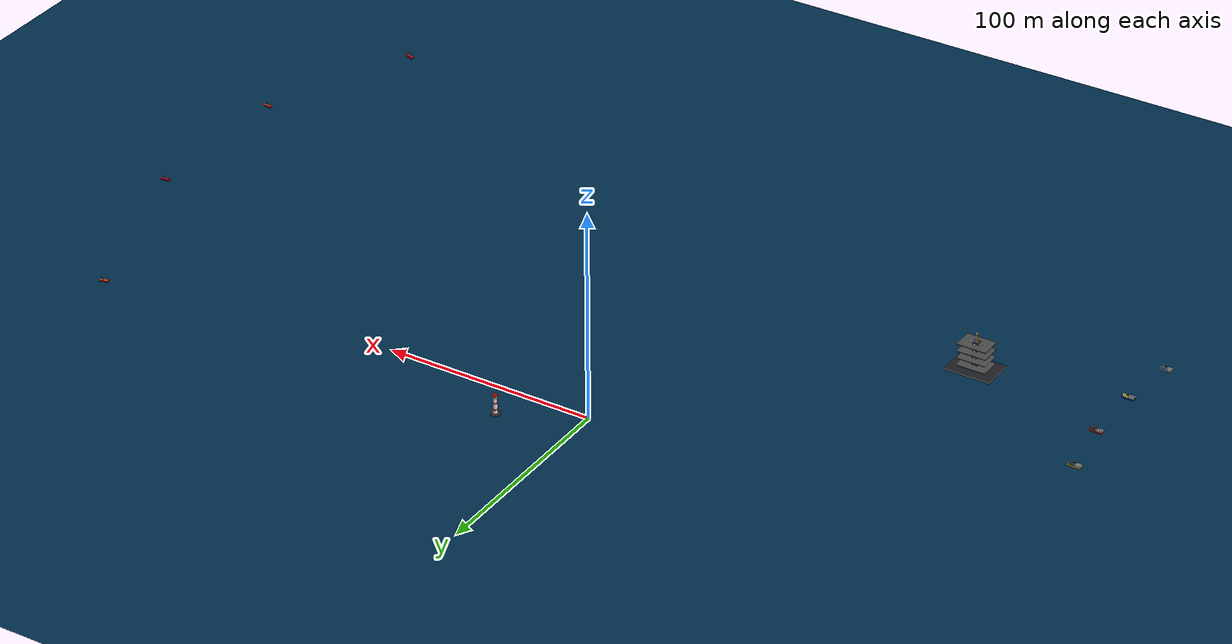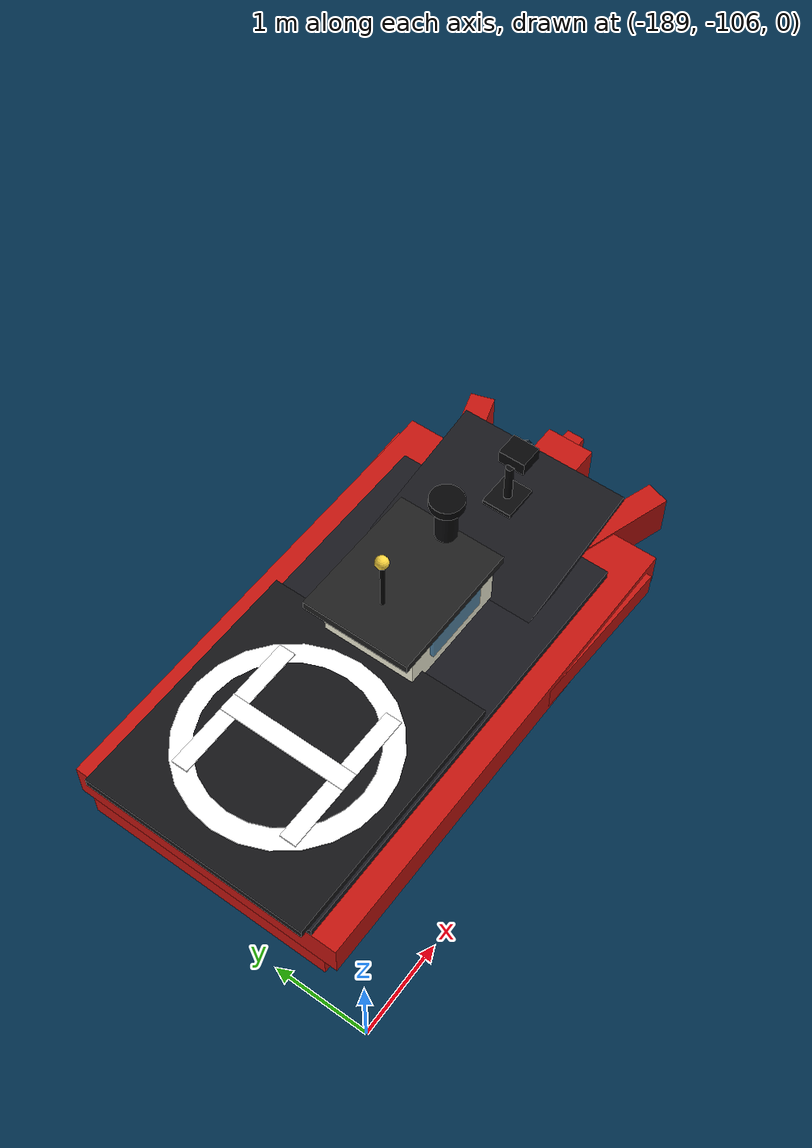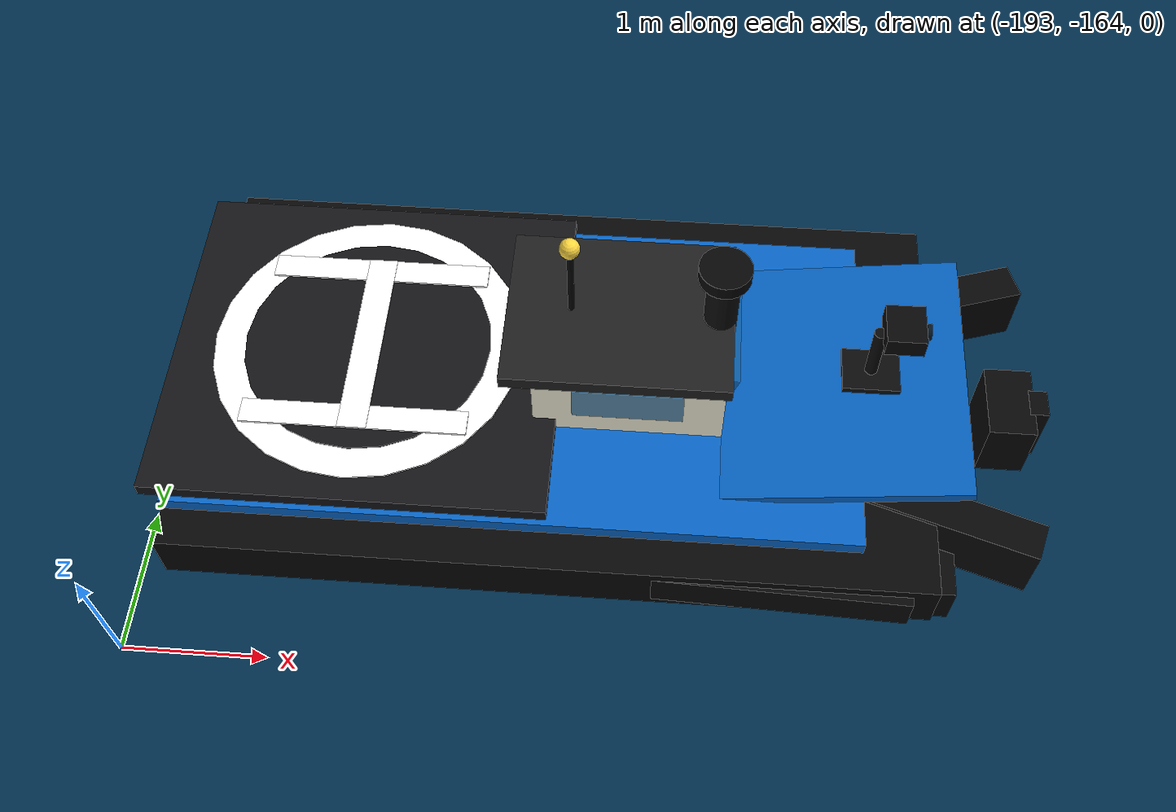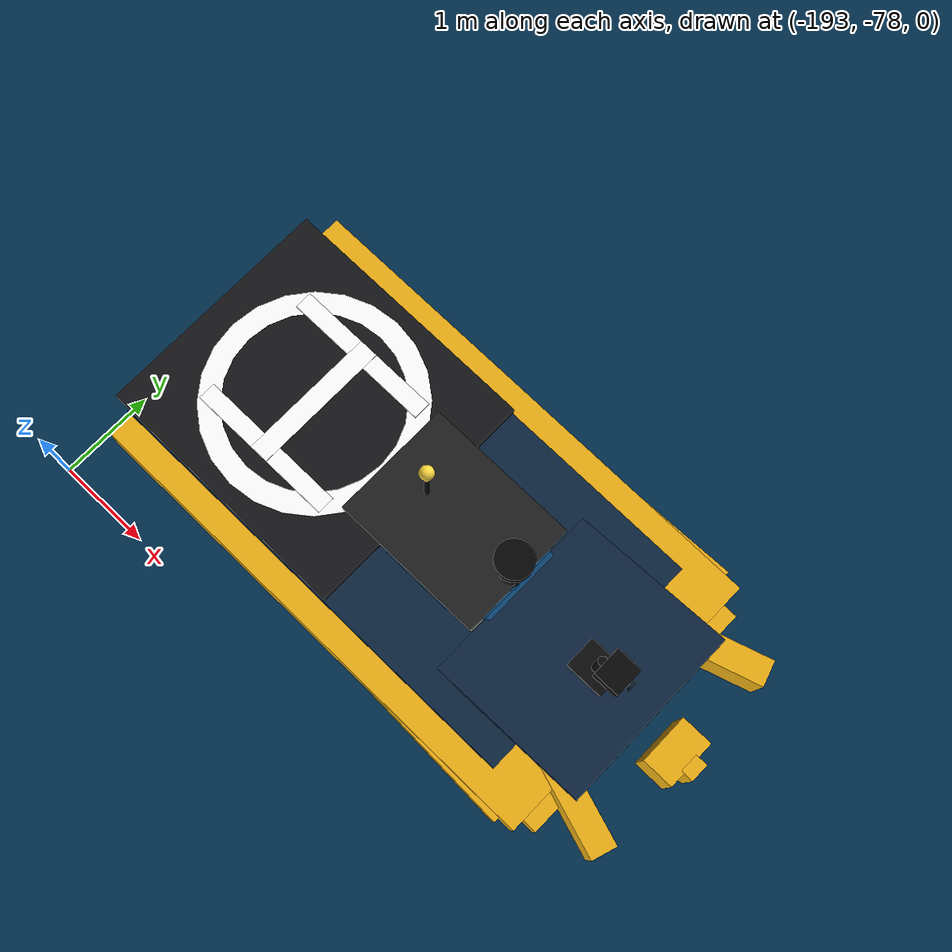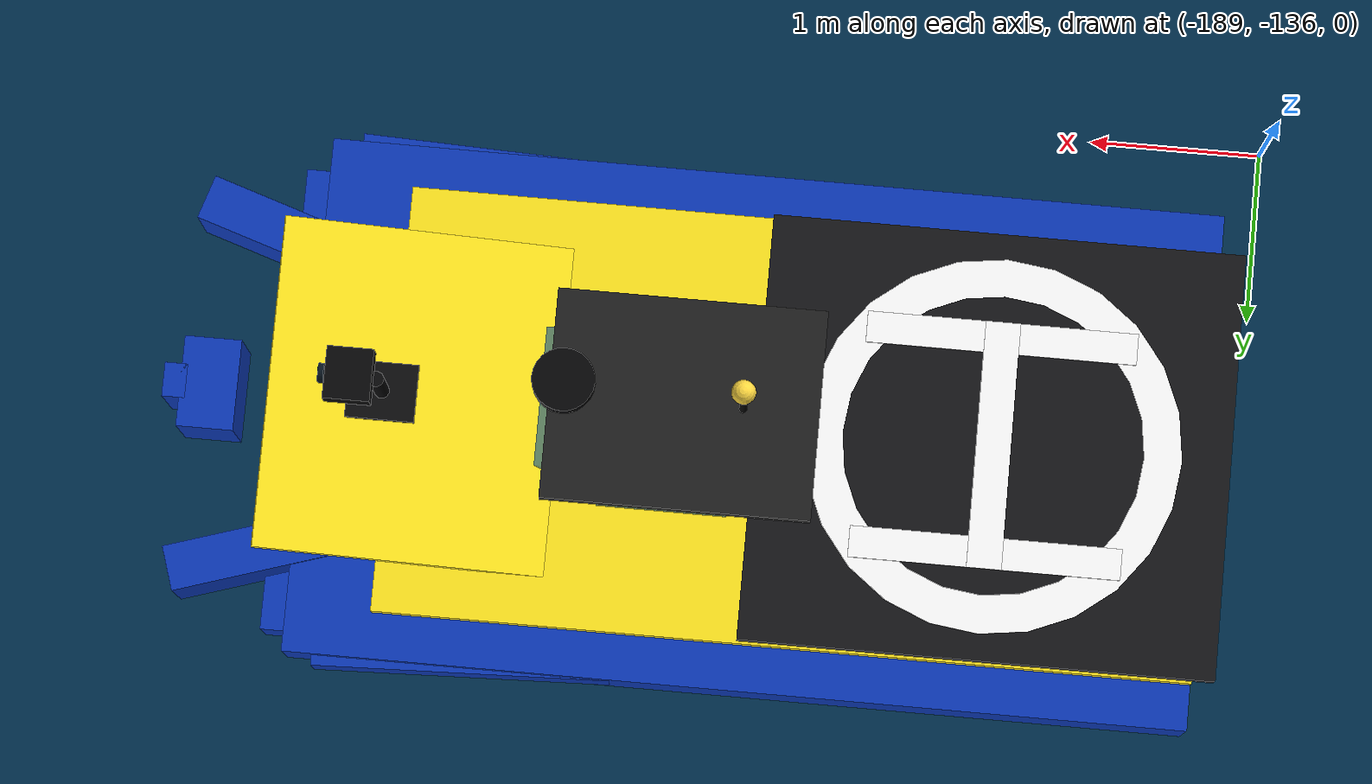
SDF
<sdf version="1.10">
 <world name="open_ocean_defense_sim">
  <plugin filename="gz-sim-physics-system" name="gz::sim::systems::Physics"/>
  <plugin filename="gz-sim-user-commands-system" name="gz::sim::systems::UserCommands"/>
  <plugin filename="gz-sim-scene-broadcaster-system" name="gz::sim::systems::SceneBroadcaster"/>
  <plugin filename="gz-sim-contact-system" name="gz::sim::systems::Contact"/>
  <plugin filename="gz-sim-imu-system" name="gz::sim::systems::Imu"/>
  <plugin filename="gz-sim-air-pressure-system" name="gz::sim::systems::AirPressure"/>
  <plugin filename="gz-sim-air-speed-system" name="gz::sim::systems::AirSpeed"/>
  <plugin filename="gz-sim-apply-link-wrench-system" name="gz::sim::systems::ApplyLinkWrench"/>
  <plugin filename="gz-sim-navsat-system" name="gz::sim::systems::NavSat"/>
  <plugin filename="gz-sim-magnetometer-system" name="gz::sim::systems::Magnetometer"/>
  <plugin filename="gz-sim-sensors-system" name="gz::sim::systems::Sensors">
   <render_engine>ogre2</render_engine>
  </plugin>
  <physics type="ode">
   <max_step_size>0.004</max_step_size>
   <real_time_factor>1</real_time_factor>
   <real_time_update_rate>250</real_time_update_rate>
  </physics>
  <gravity>0 0 -9.8</gravity>
  <magnetic_field>6.0e-06 2.3e-05 -4.2e-05</magnetic_field>
  <atmosphere type="adiabatic"/>
  <scene>
   <grid>false</grid>
   <ambient>0.82 0.84 0.86 1</ambient>
   <background>1 1 1 1</background>
   <shadows>true</shadows>
  </scene>
  <spherical_coordinates>
   <surface_model>EARTH_WGS84</surface_model>
   <world_frame_orientation>ENU</world_frame_orientation>
   <latitude_deg>47.397971057728974</latitude_deg>
   <longitude_deg>8.5461637398001464</longitude_deg>
   <elevation>0</elevation>
   <heading_deg>0</heading_deg>
  </spherical_coordinates>
  <model name="ocean_plane">
   <static>true</static>
   <link name="ocean_link">
    <visual name="ocean_visual">
     <pose>0 0 -0.02 0 0 0</pose>
     <geometry><plane><normal>0 0 1</normal><size>1000 1000</size></plane></geometry>
     <material>
      <ambient>0 0.08 0.16 0.45</ambient>
      <diffuse>0 0.18 0.3 0.45</diffuse>
      <specular>0.03 0.05 0.06 1</specular>
     </material>
    </visual>
    <collision name="ocean_collision">
     <geometry><plane><normal>0 0 1</normal><size>1000 1000</size></plane></geometry>
    </collision>
   </link>
  </model>
  <model name="navigation_lighthouse">
   <static>true</static>
   <pose>35 18 0 0 0 0</pose>
   <link name="lighthouse_link">
    <collision name="base_collision">
     <pose>0 0 0.3 0 0 0</pose>
     <geometry><cylinder><radius>2.2</radius><length>0.6</length></cylinder></geometry>
    </collision>
    <visual name="base_visual">
     <pose>0 0 0.3 0 0 0</pose>
     <geometry><cylinder><radius>2.2</radius><length>0.6</length></cylinder></geometry>
     <material>
      <ambient>0.12 0.12 0.12 1</ambient>
      <diffuse>0.18 0.18 0.16 1</diffuse>
      <specular>0.05 0.05 0.05 1</specular>
     </material>
    </visual>
    <collision name="tower_collision">
     <pose>0 0 4.4 0 0 0</pose>
     <geometry><cylinder><radius>0.85</radius><length>8.2</length></cylinder></geometry>
    </collision>
    <visual name="tower_white_visual">
     <pose>0 0 4.4 0 0 0</pose>
     <geometry><cylinder><radius>0.85</radius><length>8.2</length></cylinder></geometry>
     <material>
      <ambient>0.85 0.83 0.76 1</ambient>
      <diffuse>0.95 0.93 0.84 1</diffuse>
      <specular>0.2 0.2 0.18 1</specular>
     </material>
    </visual>
    <visual name="red_band_lower_visual">
     <pose>0 0 2.7 0 0 0</pose>
     <geometry><cylinder><radius>0.88</radius><length>0.65</length></cylinder></geometry>
     <material>
      <ambient>0.55 0.04 0.03 1</ambient>
      <diffuse>0.85 0.06 0.04 1</diffuse>
      <specular>0.15 0.03 0.03 1</specular>
     </material>
    </visual>
    <visual name="red_band_upper_visual">
     <pose>0 0 5.8 0 0 0</pose>
     <geometry><cylinder><radius>0.88</radius><length>0.65</length></cylinder></geometry>
     <material>
      <ambient>0.55 0.04 0.03 1</ambient>
      <diffuse>0.85 0.06 0.04 1</diffuse>
      <specular>0.15 0.03 0.03 1</specular>
     </material>
    </visual>
    <visual name="lantern_room_visual">
     <pose>0 0 8.8 0 0 0</pose>
     <geometry><cylinder><radius>1.05</radius><length>0.9</length></cylinder></geometry>
     <material>
      <ambient>0.95 0.82 0.32 0.85</ambient>
      <diffuse>1 0.88 0.4 0.85</diffuse>
      <specular>1 0.95 0.7 1</specular>
     </material>
    </visual>
    <visual name="roof_visual">
     <pose>0 0 9.55 0 0 0</pose>
     <geometry><cylinder><radius>1.2</radius><length>0.45</length></cylinder></geometry>
     <material>
      <ambient>0.45 0.02 0.02 1</ambient>
      <diffuse>0.7 0.03 0.03 1</diffuse>
      <specular>0.18 0.04 0.04 1</specular>
     </material>
    </visual>
    <light name="beacon_light" type="point">
     <pose>0 0 8.95 0 0 0</pose>
     <cast_shadows>false</cast_shadows>
     <intensity>3</intensity>
     <diffuse>1 0.86 0.35 1</diffuse>
     <specular>1 0.9 0.55 1</specular>
     <attenuation>
      <range>80</range>
      <constant>0.6</constant>
      <linear>0.02</linear>
      <quadratic>0.001</quadratic>
     </attenuation>
    </light>
   </link>
  </model>
  <include>
   <name>defense_base_platform</name>
   <pose>-120 -120 0 0 0 0</pose>
   <uri>model://four_level_uav_platform</uri>
  </include>
  <include><name>own_01</name><pose>-190 -162 0.35 0 0 0</pose><uri>model://defense_own_01_boat</uri></include>
  <include><name>own_02</name><pose>-186 -134 0.35 0 0 0</pose><uri>model://defense_own_02_boat</uri></include>
  <include><name>own_03</name><pose>-186 -104 0.35 0 0 0</pose><uri>model://defense_own_03_boat</uri></include>
  <include><name>own_04</name><pose>-190 -76 0.35 0 0 0</pose><uri>model://defense_own_04_boat</uri></include>
  <include>
   <name>enemy_01</name>
   <pose>240 -220 0.35 0 0 2.85</pose>
   <uri>model://defense_enemy_01_boat</uri>
  </include>
  <include>
   <name>enemy_02</name>
   <pose>270 -145 0.35 0 0 3.05</pose>
   <uri>model://defense_enemy_02_boat</uri>
  </include>
  <include>
   <name>enemy_03</name>
   <pose>270 -65 0.35 0 0 -3.05</pose>
   <uri>model://defense_enemy_03_boat</uri>
  </include>
  <include>
   <name>enemy_04</name>
   <pose>240 20 0.35 0 0 -2.75</pose>
   <uri>model://defense_enemy_04_boat</uri>
  </include>
  <light name="directionallight" type="directional">
   <pose>0 0 30 0 0 0</pose>
   <intensity>1</intensity>
   <direction>-0.35 0.15 -0.92</direction>
   <diffuse>0.85 0.85 0.82 1</diffuse>
   <specular>0.2 0.2 0.2 1</specular>
  </light>
 </world>
</sdf>

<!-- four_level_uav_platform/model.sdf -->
<sdf version="1.10">
  <model name="four_level_uav_platform">
    <static>true</static>
    <link name="structure">
      <collision name="base_collision">
        <pose>0 0 0.35 0 0 0</pose>
        <geometry>
          <box>
            <size>22 16 0.7</size>
          </box>
        </geometry>
      </collision>
      <visual name="base_float">
        <pose>0 0 0.35 0 0 0</pose>
        <geometry>
          <box>
            <size>22 16 0.7</size>
          </box>
        </geometry>
        <material>
          <ambient>0.05 0.055 0.06 1</ambient>
          <diffuse>0.12 0.13 0.14 1</diffuse>
          <specular>0.18 0.18 0.18 1</specular>
        </material>
      </visual>
      <visual name="green_base_marker">
        <pose>0 0 0.74 0 0 0</pose>
        <geometry>
          <cylinder>
            <radius>3.4</radius>
            <length>0.05</length>
          </cylinder>
        </geometry>
        <material>
          <ambient>0.0 0.55 0.18 1</ambient>
          <diffuse>0.0 0.85 0.30 1</diffuse>
        </material>
      </visual>
      <visual name="tower_core">
        <pose>0 0 7.2 0 0 0</pose>
        <geometry>
          <box>
            <size>2.8 2.8 13.0</size>
          </box>
        </geometry>
        <material>
          <ambient>0.10 0.11 0.12 1</ambient>
          <diffuse>0.22 0.24 0.26 1</diffuse>
        </material>
      </visual>
      <visual name="mast">
        <pose>0 0 15.2 0 0 0</pose>
        <geometry>
          <cylinder>
            <radius>0.15</radius>
            <length>4.2</length>
          </cylinder>
        </geometry>
        <material>
          <ambient>0.8 0.72 0.08 1</ambient>
          <diffuse>1 0.90 0.10 1</diffuse>
        </material>
      </visual>
      <visual name="top_light">
        <pose>0 0 17.5 0 0 0</pose>
        <geometry>
          <sphere>
            <radius>0.45</radius>
          </sphere>
        </geometry>
        <material>
          <ambient>1 0.9 0.1 1</ambient>
          <diffuse>1 0.9 0.1 1</diffuse>
          <emissive>1 0.75 0.05 1</emissive>
        </material>
      </visual>
      <light name="platform_light" type="point">
        <pose>0 0 17.5 0 0 0</pose>
        <cast_shadows>false</cast_shadows>
        <intensity>1.2</intensity>
        <diffuse>1 0.85 0.35 1</diffuse>
        <attenuation>
          <range>80</range>
          <constant>0.6</constant>
          <linear>0.03</linear>
          <quadratic>0.001</quadratic>
        </attenuation>
      </light>
      <visual name="level_1_deck">
        <pose>0 0 2.2 0 0 0</pose>
        <geometry><box><size>14 10 0.28</size></box></geometry>
        <material><ambient>0.16 0.16 0.16 1</ambient><diffuse>0.30 0.30 0.30 1</diffuse></material>
      </visual>
      <visual name="level_2_deck">
        <pose>0 0 5.7 0 0 0</pose>
        <geometry><box><size>14 10 0.28</size></box></geometry>
        <material><ambient>0.16 0.16 0.16 1</ambient><diffuse>0.30 0.30 0.30 1</diffuse></material>
      </visual>
      <visual name="level_3_deck">
        <pose>0 0 9.2 0 0 0</pose>
        <geometry><box><size>14 10 0.28</size></box></geometry>
        <material><ambient>0.16 0.16 0.16 1</ambient><diffuse>0.30 0.30 0.30 1</diffuse></material>
      </visual>
      <visual name="level_4_deck">
        <pose>0 0 12.7 0 0 0</pose>
        <geometry><box><size>14 10 0.28</size></box></geometry>
        <material><ambient>0.16 0.16 0.16 1</ambient><diffuse>0.30 0.30 0.30 1</diffuse></material>
      </visual>
      <visual name="h_1_a"><pose>0 0 2.36 0 0 0</pose><geometry><box><size>5.8 0.42 0.06</size></box></geometry><material><ambient>1 1 1 1</ambient><diffuse>1 1 1 1</diffuse></material></visual>
      <visual name="h_1_b"><pose>0 0 2.37 0 0 1.5708</pose><geometry><box><size>4.2 0.42 0.06</size></box></geometry><material><ambient>1 1 1 1</ambient><diffuse>1 1 1 1</diffuse></material></visual>
      <visual name="h_2_a"><pose>0 0 5.86 0 0 0</pose><geometry><box><size>5.8 0.42 0.06</size></box></geometry><material><ambient>1 1 1 1</ambient><diffuse>1 1 1 1</diffuse></material></visual>
      <visual name="h_2_b"><pose>0 0 5.87 0 0 1.5708</pose><geometry><box><size>4.2 0.42 0.06</size></box></geometry><material><ambient>1 1 1 1</ambient><diffuse>1 1 1 1</diffuse></material></visual>
      <visual name="h_3_a"><pose>0 0 9.36 0 0 0</pose><geometry><box><size>5.8 0.42 0.06</size></box></geometry><material><ambient>1 1 1 1</ambient><diffuse>1 1 1 1</diffuse></material></visual>
      <visual name="h_3_b"><pose>0 0 9.37 0 0 1.5708</pose><geometry><box><size>4.2 0.42 0.06</size></box></geometry><material><ambient>1 1 1 1</ambient><diffuse>1 1 1 1</diffuse></material></visual>
      <visual name="h_4_a"><pose>0 0 12.86 0 0 0</pose><geometry><box><size>5.8 0.42 0.06</size></box></geometry><material><ambient>1 1 1 1</ambient><diffuse>1 1 1 1</diffuse></material></visual>
      <visual name="h_4_b"><pose>0 0 12.87 0 0 1.5708</pose><geometry><box><size>4.2 0.42 0.06</size></box></geometry><material><ambient>1 1 1 1</ambient><diffuse>1 1 1 1</diffuse></material></visual>
    </link>
  </model>
</sdf>

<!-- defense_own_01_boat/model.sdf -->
<sdf version="1.8">
  <model name="defense_own_01_boat">
    <pose>0 0 0.4375 0 0 0</pose>

    <link name="hull">
      <enable_wind>true</enable_wind>
      <inertial>
        <mass>150.0</mass>
        <inertia>
          <ixx>85.0</ixx>
          <iyy>180.0</iyy>
          <izz>220.0</izz>
          <ixy>0</ixy>
          <ixz>0</ixz>
          <iyz>0</iyz>
        </inertia>
      </inertial>

      <collision name="hull_collision">
        <pose>0 0 -0.0625 0 0 0</pose>
        <geometry>
          <box>
            <size>5.61 3.135 0.625</size>
          </box>
        </geometry>
      </collision>

      <visual name="lower_hull">
        <pose>-0.0825 0 -0.2 0 0 0</pose>
        <geometry>
          <box>
            <size>5.3625 2.7225 0.35</size>
          </box>
        </geometry>
        <material>
          <ambient>0.015 0.015 0.018 1</ambient>
          <diffuse>0.025 0.025 0.030 1</diffuse>
          <specular>0.1 0.1 0.1 1</specular>
        </material>
      </visual>

      <visual name="upper_hull">
        <pose>-0.165 0 0.0625 0 0 0</pose>
        <geometry>
          <box>
            <size>5.1975 3.003 0.4</size>
          </box>
        </geometry>
        <material>
          <ambient>0.015 0.015 0.018 1</ambient>
          <diffuse>0.025 0.025 0.030 1</diffuse>
          <specular>0.18 0.18 0.2 1</specular>
        </material>
      </visual>

      <visual name="bow_side_left">
        <pose>2.409 0.858 0.05 0 0 0.31</pose>
        <geometry>
          <box>
            <size>1.518 0.264 0.475</size>
          </box>
        </geometry>
        <material>
          <ambient>0.015 0.015 0.018 1</ambient>
          <diffuse>0.025 0.025 0.030 1</diffuse>
          <specular>0.18 0.18 0.2 1</specular>
        </material>
      </visual>

      <visual name="bow_side_right">
        <pose>2.409 -0.858 0.05 0 0 -0.31</pose>
        <geometry>
          <box>
            <size>1.518 0.264 0.475</size>
          </box>
        </geometry>
        <material>
          <ambient>0.015 0.015 0.018 1</ambient>
          <diffuse>0.025 0.025 0.030 1</diffuse>
          <specular>0.18 0.18 0.2 1</specular>
        </material>
      </visual>

      <visual name="bow_center_nose">
        <pose>3.003 0 0.05 0 0 0</pose>
        <geometry>
          <box>
            <size>0.33 0.528 0.5</size>
          </box>
        </geometry>
        <material>
          <ambient>0.015 0.015 0.018 1</ambient>
          <diffuse>0.025 0.025 0.030 1</diffuse>
          <specular>0.16 0.16 0.18 1</specular>
        </material>
      </visual>

      <visual name="bow_keel_line">
        <pose>2.5575 0 -0.425 0 1.5708 0</pose>
        <geometry>
          <cylinder>
            <radius>0.035</radius>
            <length>0.9</length>
          </cylinder>
        </geometry>
        <material>
          <ambient>0.006 0.006 0.008 1</ambient>
          <diffuse>0.012 0.012 0.014 1</diffuse>
        </material>
      </visual>

      <visual name="foredeck_slope">
        <pose>1.7325 0 0.45 0 -0.16 0</pose>
        <geometry>
          <box>
            <size>1.815 1.914 0.06875</size>
          </box>
        </geometry>
        <material>
          <ambient>0.02 0.18 0.35 1</ambient>
          <diffuse>0.03 0.40 0.78 1</diffuse>
          <specular>0.08 0.08 0.08 1</specular>
        </material>
      </visual>

      <visual name="bow_stem">
        <pose>3.201 0 0.0375 0 0 0</pose>
        <geometry>
          <box>
            <size>0.132 0.198 0.525</size>
          </box>
        </geometry>
        <material>
          <ambient>0.015 0.015 0.018 1</ambient>
          <diffuse>0.025 0.025 0.030 1</diffuse>
          <specular>0.16 0.16 0.18 1</specular>
        </material>
      </visual>

      <visual name="hull_side_fairing_left">
        <pose>0.0825 1.419 0.05 0 0 0.035</pose>
        <geometry>
          <box>
            <size>4.3725 0.132 0.275</size>
          </box>
        </geometry>
        <material>
          <ambient>0.015 0.015 0.018 1</ambient>
          <diffuse>0.025 0.025 0.030 1</diffuse>
          <specular>0.14 0.14 0.16 1</specular>
        </material>
      </visual>

      <visual name="hull_side_fairing_right">
        <pose>0.0825 -1.419 0.05 0 0 -0.035</pose>
        <geometry>
          <box>
            <size>4.3725 0.132 0.275</size>
          </box>
        </geometry>
        <material>
          <ambient>0.015 0.015 0.018 1</ambient>
          <diffuse>0.025 0.025 0.030 1</diffuse>
          <specular>0.14 0.14 0.16 1</specular>
        </material>
      </visual>

      <visual name="deck">
        <pose>-0.4125 0 0.3125 0 0 0</pose>
        <geometry>
          <box>
            <size>4.7025 2.475 0.1</size>
          </box>
        </geometry>
        <material>
          <ambient>0.02 0.18 0.35 1</ambient>
          <diffuse>0.03 0.40 0.78 1</diffuse>
          <specular>0.08 0.08 0.08 1</specular>
        </material>
      </visual>

      <visual name="cabin_body">
        <pose>0.33 0 0.725 0 0 0</pose>
        <geometry>
          <box>
            <size>1.287 1.023 0.6</size>
          </box>
        </geometry>
        <material>
          <ambient>0.86 0.86 0.8 1</ambient>
          <diffuse>0.96 0.95 0.86 1</diffuse>
          <specular>0.28 0.28 0.24 1</specular>
        </material>
      </visual>

      <visual name="front_window">
        <pose>0.99 0 0.8 0 0.28 0</pose>
        <geometry>
          <box>
            <size>0.05775 0.792 0.3</size>
          </box>
        </geometry>
        <material>
          <ambient>0.05 0.22 0.36 0.65</ambient>
          <diffuse>0.08 0.38 0.62 0.65</diffuse>
          <specular>0.9 0.95 1 1</specular>
        </material>
      </visual>

      <visual name="left_window">
        <pose>0.33 0.53625 0.8 0 0 0</pose>
        <geometry>
          <box>
            <size>0.7425 0.04125 0.275</size>
          </box>
        </geometry>
        <material>
          <ambient>0.05 0.22 0.36 0.65</ambient>
          <diffuse>0.08 0.38 0.62 0.65</diffuse>
          <specular>0.9 0.95 1 1</specular>
        </material>
      </visual>

      <visual name="right_window">
        <pose>0.33 -0.53625 0.8 0 0 0</pose>
        <geometry>
          <box>
            <size>0.7425 0.04125 0.275</size>
          </box>
        </geometry>
        <material>
          <ambient>0.05 0.22 0.36 0.65</ambient>
          <diffuse>0.08 0.38 0.62 0.65</diffuse>
          <specular>0.9 0.95 1 1</specular>
        </material>
      </visual>

      <visual name="cabin_roof">
        <pose>0.2475 0 1.0625 0 0 0</pose>
        <geometry>
          <box>
            <size>1.518 1.188 0.1</size>
          </box>
        </geometry>
        <material>
          <ambient>0.08 0.08 0.08 1</ambient>
          <diffuse>0.12 0.12 0.12 1</diffuse>
          <specular>0.18 0.18 0.18 1</specular>
        </material>
      </visual>

      <collision name="landing_pad_collision">
        <pose>-1.518 0 0.45 0 0 0</pose>
        <geometry>
          <box>
            <size>2.805 2.5575 0.3</size>
          </box>
        </geometry>
        <surface>
          <contact>
            <ode>
              <min_depth>0.001</min_depth>
              <max_vel>0</max_vel>
            </ode>
          </contact>
          <friction>
            <ode>
              <mu>1.5</mu>
              <mu2>1.5</mu2>
            </ode>
          </friction>
        </surface>
      </collision>

      <visual name="landing_pad_visual">
        <pose>-1.518 0 0.475 0 0 0</pose>
        <geometry>
          <box>
            <size>2.72 2.46 0.1</size>
          </box>
        </geometry>
        <material>
          <ambient>0.04 0.04 0.045 1</ambient>
          <diffuse>0.08 0.08 0.09 1</diffuse>
          <specular>0.08 0.08 0.08 1</specular>
        </material>
      </visual>

      <visual name="landing_pad_ring">
        <pose>-1.518 0 0.54375 0 0 0</pose>
        <geometry>
          <cylinder>
            <radius>1.08</radius>
            <length>0.015</length>
          </cylinder>
        </geometry>
        <material>
          <ambient>1 1 1 1</ambient>
          <diffuse>1 1 1 1</diffuse>
        </material>
      </visual>

      <visual name="landing_pad_center">
        <pose>-1.518 0 0.55625 0 0 0</pose>
        <geometry>
          <cylinder>
            <radius>0.86</radius>
            <length>0.0175</length>
          </cylinder>
        </geometry>
        <material>
          <ambient>0.04 0.04 0.045 1</ambient>
          <diffuse>0.08 0.08 0.09 1</diffuse>
        </material>
      </visual>

      <visual name="landing_h_left">
        <pose>-1.518 0.62 0.5725 0 0 0</pose>
        <geometry>
          <box>
            <size>1.55 0.18 0.015</size>
          </box>
        </geometry>
        <material>
          <ambient>1 1 1 1</ambient>
          <diffuse>1 1 1 1</diffuse>
        </material>
      </visual>

      <visual name="landing_h_right">
        <pose>-1.518 -0.62 0.5725 0 0 0</pose>
        <geometry>
          <box>
            <size>1.55 0.18 0.015</size>
          </box>
        </geometry>
        <material>
          <ambient>1 1 1 1</ambient>
          <diffuse>1 1 1 1</diffuse>
        </material>
      </visual>

      <visual name="landing_h_crossbar">
        <pose>-1.518 0 0.5775 0 0 0</pose>
        <geometry>
          <box>
            <size>0.2 1.42 0.015</size>
          </box>
        </geometry>
        <material>
          <ambient>1 1 1 1</ambient>
          <diffuse>1 1 1 1</diffuse>
        </material>
      </visual>

      <visual name="mast">
        <pose>-0.0825 0 1.375 0 0 0</pose>
        <geometry>
          <cylinder>
            <radius>0.0225</radius>
            <length>0.6875</length>
          </cylinder>
        </geometry>
        <material>
          <ambient>0.02 0.02 0.02 1</ambient>
          <diffuse>0.02 0.02 0.02 1</diffuse>
        </material>
      </visual>

      <visual name="nav_light">
        <pose>-0.0825 0 1.7375 0 0 0</pose>
        <geometry>
          <sphere>
            <radius>0.06875</radius>
          </sphere>
        </geometry>
        <material>
          <ambient>1 0.85 0.25 1</ambient>
          <diffuse>1 0.85 0.25 1</diffuse>
          <specular>1 0.9 0.5 1</specular>
        </material>
      </visual>

      <visual name="lidar_mount">
        <pose>0.9075 0 1.175 0 0 0</pose>
        <geometry>
          <cylinder>
            <radius>0.1125</radius>
            <length>0.775</length>
          </cylinder>
        </geometry>
        <material>
          <ambient>0.02 0.02 0.022 1</ambient>
          <diffuse>0.04 0.04 0.045 1</diffuse>
          <specular>0.2 0.2 0.22 1</specular>
        </material>
      </visual>

      <visual name="lidar_body">
        <pose>0.9075 0 1.5875 0 0 0</pose>
        <geometry>
          <cylinder>
            <radius>0.175</radius>
            <length>0.1</length>
          </cylinder>
        </geometry>
        <material>
          <ambient>0.01 0.01 0.012 1</ambient>
          <diffuse>0.02 0.02 0.024 1</diffuse>
          <specular>0.35 0.35 0.38 1</specular>
        </material>
      </visual>

      <visual name="front_camera_mount_base">
        <pose>1.98 0 0.56875 0 0 0</pose>
        <geometry>
          <box>
            <size>0.396 0.33 0.05</size>
          </box>
        </geometry>
        <material>
          <ambient>0.025 0.025 0.028 1</ambient>
          <diffuse>0.04 0.04 0.045 1</diffuse>
          <specular>0.18 0.18 0.2 1</specular>
        </material>
      </visual>

      <visual name="front_camera_mount_post">
        <pose>1.98 0 0.8125 0 0 0</pose>
        <geometry>
          <cylinder>
            <radius>0.04375</radius>
            <length>0.4375</length>
          </cylinder>
        </geometry>
        <material>
          <ambient>0.018 0.018 0.02 1</ambient>
          <diffuse>0.03 0.03 0.034 1</diffuse>
          <specular>0.18 0.18 0.2 1</specular>
        </material>
      </visual>

      <visual name="front_camera_body">
        <pose>2.1285 0 1.075 0 0 0</pose>
        <geometry>
          <box>
            <size>0.264 0.297 0.15</size>
          </box>
        </geometry>
        <material>
          <ambient>0.015 0.015 0.018 1</ambient>
          <diffuse>0.025 0.025 0.03 1</diffuse>
          <specular>0.2 0.2 0.22 1</specular>
        </material>
      </visual>

      <visual name="front_camera_lens">
        <pose>2.28525 0 1.075 0 1.5708 0</pose>
        <geometry>
          <cylinder>
            <radius>0.05625</radius>
            <length>0.03125</length>
          </cylinder>
        </geometry>
        <material>
          <ambient>0.02 0.04 0.06 1</ambient>
          <diffuse>0.03 0.08 0.12 1</diffuse>
          <specular>0.8 0.9 1 1</specular>
        </material>
      </visual>

      <sensor name="front_camera" type="camera">
        <pose>2.31825 0 1.075 0 0 0</pose>
        <topic>/defense/own_01/front_camera</topic>
        <update_rate>30</update_rate>
        <camera>
          <horizontal_fov>1.047</horizontal_fov>
          <image>
            <width>320</width>
            <height>180</height>
            <format>R8G8B8</format>
          </image>
          <clip>
            <near>0.05</near>
            <far>200</far>
          </clip>
        </camera>
        <always_on>true</always_on>
        <visualize>false</visualize>
      </sensor>

      <sensor name="front_lidar" type="gpu_lidar">
        <gz_frame_id>own_01/hull/front_lidar</gz_frame_id>
        <pose>0.9075 0 1.5625 0 0 0</pose>
        <topic>/defense/own_01/scan</topic>
        <update_rate>10</update_rate>
        <ray>
          <scan>
            <horizontal>
              <samples>361</samples>
              <resolution>1</resolution>
              <min_angle>-1.5708</min_angle>
              <max_angle>1.5708</max_angle>
            </horizontal>
          </scan>
          <range>
            <min>0.35</min>
            <max>80</max>
            <resolution>0.02</resolution>
          </range>
          <noise>
            <type>gaussian</type>
            <mean>0</mean>
            <stddev>0.01</stddev>
          </noise>
          <visibility_mask>0x01</visibility_mask>
        </ray>
        <always_on>true</always_on>
        <visualize>false</visualize>
      </sensor>
    </link>

    <plugin
      filename="gz-sim-velocity-control-system"
      name="gz::sim::systems::VelocityControl">
      <topic>/model/own_01/cmd_vel</topic>
      <control_linear_velocity>true</control_linear_velocity>
      <control_angular_velocity>true</control_angular_velocity>
    </plugin>

    <plugin
      filename="gz-sim-pose-publisher-system"
      name="gz::sim::systems::PosePublisher">
      <publish_model_pose>true</publish_model_pose>
      <publish_link_pose>false</publish_link_pose>
      <publish_collision_pose>false</publish_collision_pose>
      <publish_visual_pose>false</publish_visual_pose>
      <publish_nested_model_pose>false</publish_nested_model_pose>
      <publish_sensor_pose>false</publish_sensor_pose>
      <use_pose_vector_msg>false</use_pose_vector_msg>
      /defense/own_01/pose
      <update_frequency>30</update_frequency>
    </plugin>

    <plugin
      filename="libBoatWaveFollower.so"
      name="gz::sim::systems::BoatWaveFollower">
      <mean_z>0.55</mean_z>
      <heave_amplitude>0.11</heave_amplitude>
      <roll_amplitude>0.055</roll_amplitude>
      <pitch_amplitude>0.045</pitch_amplitude>
      <primary_frequency>1.1</primary_frequency>
      <secondary_frequency>1.7</secondary_frequency>
      <wave_number_x>0.35</wave_number_x>
      <wave_number_y>0.22</wave_number_y>
    </plugin>
  </model>
</sdf>

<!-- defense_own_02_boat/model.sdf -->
<sdf version="1.8">
  <model name="defense_own_02_boat">
    <pose>0 0 0.4375 0 0 0</pose>

    <link name="hull">
      <enable_wind>true</enable_wind>
      <inertial>
        <mass>150.0</mass>
        <inertia>
          <ixx>85.0</ixx>
          <iyy>180.0</iyy>
          <izz>220.0</izz>
          <ixy>0</ixy>
          <ixz>0</ixz>
          <iyz>0</iyz>
        </inertia>
      </inertial>

      <collision name="hull_collision">
        <pose>0 0 -0.0625 0 0 0</pose>
        <geometry>
          <box>
            <size>5.61 3.135 0.625</size>
          </box>
        </geometry>
      </collision>

      <visual name="lower_hull">
        <pose>-0.0825 0 -0.2 0 0 0</pose>
        <geometry>
          <box>
            <size>5.3625 2.7225 0.35</size>
          </box>
        </geometry>
        <material>
          <ambient>0.02 0.10 0.28 1</ambient>
          <diffuse>0.04 0.22 0.72 1</diffuse>
          <specular>0.1 0.1 0.1 1</specular>
        </material>
      </visual>

      <visual name="upper_hull">
        <pose>-0.165 0 0.0625 0 0 0</pose>
        <geometry>
          <box>
            <size>5.1975 3.003 0.4</size>
          </box>
        </geometry>
        <material>
          <ambient>0.02 0.10 0.28 1</ambient>
          <diffuse>0.04 0.22 0.72 1</diffuse>
          <specular>0.18 0.18 0.2 1</specular>
        </material>
      </visual>

      <visual name="bow_side_left">
        <pose>2.409 0.858 0.05 0 0 0.31</pose>
        <geometry>
          <box>
            <size>1.518 0.264 0.475</size>
          </box>
        </geometry>
        <material>
          <ambient>0.02 0.10 0.28 1</ambient>
          <diffuse>0.04 0.22 0.72 1</diffuse>
          <specular>0.18 0.18 0.2 1</specular>
        </material>
      </visual>

      <visual name="bow_side_right">
        <pose>2.409 -0.858 0.05 0 0 -0.31</pose>
        <geometry>
          <box>
            <size>1.518 0.264 0.475</size>
          </box>
        </geometry>
        <material>
          <ambient>0.02 0.10 0.28 1</ambient>
          <diffuse>0.04 0.22 0.72 1</diffuse>
          <specular>0.18 0.18 0.2 1</specular>
        </material>
      </visual>

      <visual name="bow_center_nose">
        <pose>3.003 0 0.05 0 0 0</pose>
        <geometry>
          <box>
            <size>0.33 0.528 0.5</size>
          </box>
        </geometry>
        <material>
          <ambient>0.02 0.10 0.28 1</ambient>
          <diffuse>0.04 0.22 0.72 1</diffuse>
          <specular>0.16 0.16 0.18 1</specular>
        </material>
      </visual>

      <visual name="bow_keel_line">
        <pose>2.5575 0 -0.425 0 1.5708 0</pose>
        <geometry>
          <cylinder>
            <radius>0.035</radius>
            <length>0.9</length>
          </cylinder>
        </geometry>
        <material>
          <ambient>0.006 0.006 0.008 1</ambient>
          <diffuse>0.012 0.012 0.014 1</diffuse>
        </material>
      </visual>

      <visual name="foredeck_slope">
        <pose>1.7325 0 0.45 0 -0.16 0</pose>
        <geometry>
          <box>
            <size>1.815 1.914 0.06875</size>
          </box>
        </geometry>
        <material>
          <ambient>0.75 0.75 0.08 1</ambient>
          <diffuse>1.00 0.90 0.12 1</diffuse>
          <specular>0.08 0.08 0.08 1</specular>
        </material>
      </visual>

      <visual name="bow_stem">
        <pose>3.201 0 0.0375 0 0 0</pose>
        <geometry>
          <box>
            <size>0.132 0.198 0.525</size>
          </box>
        </geometry>
        <material>
          <ambient>0.02 0.10 0.28 1</ambient>
          <diffuse>0.04 0.22 0.72 1</diffuse>
          <specular>0.16 0.16 0.18 1</specular>
        </material>
      </visual>

      <visual name="hull_side_fairing_left">
        <pose>0.0825 1.419 0.05 0 0 0.035</pose>
        <geometry>
          <box>
            <size>4.3725 0.132 0.275</size>
          </box>
        </geometry>
        <material>
          <ambient>0.02 0.10 0.28 1</ambient>
          <diffuse>0.04 0.22 0.72 1</diffuse>
          <specular>0.14 0.14 0.16 1</specular>
        </material>
      </visual>

      <visual name="hull_side_fairing_right">
        <pose>0.0825 -1.419 0.05 0 0 -0.035</pose>
        <geometry>
          <box>
            <size>4.3725 0.132 0.275</size>
          </box>
        </geometry>
        <material>
          <ambient>0.02 0.10 0.28 1</ambient>
          <diffuse>0.04 0.22 0.72 1</diffuse>
          <specular>0.14 0.14 0.16 1</specular>
        </material>
      </visual>

      <visual name="deck">
        <pose>-0.4125 0 0.3125 0 0 0</pose>
        <geometry>
          <box>
            <size>4.7025 2.475 0.1</size>
          </box>
        </geometry>
        <material>
          <ambient>0.75 0.75 0.08 1</ambient>
          <diffuse>1.00 0.90 0.12 1</diffuse>
          <specular>0.08 0.08 0.08 1</specular>
        </material>
      </visual>

      <visual name="cabin_body">
        <pose>0.33 0 0.725 0 0 0</pose>
        <geometry>
          <box>
            <size>1.287 1.023 0.6</size>
          </box>
        </geometry>
        <material>
          <ambient>0.86 0.86 0.8 1</ambient>
          <diffuse>0.96 0.95 0.86 1</diffuse>
          <specular>0.28 0.28 0.24 1</specular>
        </material>
      </visual>

      <visual name="front_window">
        <pose>0.99 0 0.8 0 0.28 0</pose>
        <geometry>
          <box>
            <size>0.05775 0.792 0.3</size>
          </box>
        </geometry>
        <material>
          <ambient>0.05 0.22 0.36 0.65</ambient>
          <diffuse>0.08 0.38 0.62 0.65</diffuse>
          <specular>0.9 0.95 1 1</specular>
        </material>
      </visual>

      <visual name="left_window">
        <pose>0.33 0.53625 0.8 0 0 0</pose>
        <geometry>
          <box>
            <size>0.7425 0.04125 0.275</size>
          </box>
        </geometry>
        <material>
          <ambient>0.05 0.22 0.36 0.65</ambient>
          <diffuse>0.08 0.38 0.62 0.65</diffuse>
          <specular>0.9 0.95 1 1</specular>
        </material>
      </visual>

      <visual name="right_window">
        <pose>0.33 -0.53625 0.8 0 0 0</pose>
        <geometry>
          <box>
            <size>0.7425 0.04125 0.275</size>
          </box>
        </geometry>
        <material>
          <ambient>0.05 0.22 0.36 0.65</ambient>
          <diffuse>0.08 0.38 0.62 0.65</diffuse>
          <specular>0.9 0.95 1 1</specular>
        </material>
      </visual>

      <visual name="cabin_roof">
        <pose>0.2475 0 1.0625 0 0 0</pose>
        <geometry>
          <box>
            <size>1.518 1.188 0.1</size>
          </box>
        </geometry>
        <material>
          <ambient>0.08 0.08 0.08 1</ambient>
          <diffuse>0.12 0.12 0.12 1</diffuse>
          <specular>0.18 0.18 0.18 1</specular>
        </material>
      </visual>

      <collision name="landing_pad_collision">
        <pose>-1.518 0 0.45 0 0 0</pose>
        <geometry>
          <box>
            <size>2.805 2.5575 0.3</size>
          </box>
        </geometry>
        <surface>
          <contact>
            <ode>
              <min_depth>0.001</min_depth>
              <max_vel>0</max_vel>
            </ode>
          </contact>
          <friction>
            <ode>
              <mu>1.5</mu>
              <mu2>1.5</mu2>
            </ode>
          </friction>
        </surface>
      </collision>

      <visual name="landing_pad_visual">
        <pose>-1.518 0 0.475 0 0 0</pose>
        <geometry>
          <box>
            <size>2.72 2.46 0.1</size>
          </box>
        </geometry>
        <material>
          <ambient>0.04 0.04 0.045 1</ambient>
          <diffuse>0.08 0.08 0.09 1</diffuse>
          <specular>0.08 0.08 0.08 1</specular>
        </material>
      </visual>

      <visual name="landing_pad_ring">
        <pose>-1.518 0 0.54375 0 0 0</pose>
        <geometry>
          <cylinder>
            <radius>1.08</radius>
            <length>0.015</length>
          </cylinder>
        </geometry>
        <material>
          <ambient>1 1 1 1</ambient>
          <diffuse>1 1 1 1</diffuse>
        </material>
      </visual>

      <visual name="landing_pad_center">
        <pose>-1.518 0 0.55625 0 0 0</pose>
        <geometry>
          <cylinder>
            <radius>0.86</radius>
            <length>0.0175</length>
          </cylinder>
        </geometry>
        <material>
          <ambient>0.04 0.04 0.045 1</ambient>
          <diffuse>0.08 0.08 0.09 1</diffuse>
        </material>
      </visual>

      <visual name="landing_h_left">
        <pose>-1.518 0.62 0.5725 0 0 0</pose>
        <geometry>
          <box>
            <size>1.55 0.18 0.015</size>
          </box>
        </geometry>
        <material>
          <ambient>1 1 1 1</ambient>
          <diffuse>1 1 1 1</diffuse>
        </material>
      </visual>

      <visual name="landing_h_right">
        <pose>-1.518 -0.62 0.5725 0 0 0</pose>
        <geometry>
          <box>
            <size>1.55 0.18 0.015</size>
          </box>
        </geometry>
        <material>
          <ambient>1 1 1 1</ambient>
          <diffuse>1 1 1 1</diffuse>
        </material>
      </visual>

      <visual name="landing_h_crossbar">
        <pose>-1.518 0 0.5775 0 0 0</pose>
        <geometry>
          <box>
            <size>0.2 1.42 0.015</size>
          </box>
        </geometry>
        <material>
          <ambient>1 1 1 1</ambient>
          <diffuse>1 1 1 1</diffuse>
        </material>
      </visual>

      <visual name="mast">
        <pose>-0.0825 0 1.375 0 0 0</pose>
        <geometry>
          <cylinder>
            <radius>0.0225</radius>
            <length>0.6875</length>
          </cylinder>
        </geometry>
        <material>
          <ambient>0.02 0.02 0.02 1</ambient>
          <diffuse>0.02 0.02 0.02 1</diffuse>
        </material>
      </visual>

      <visual name="nav_light">
        <pose>-0.0825 0 1.7375 0 0 0</pose>
        <geometry>
          <sphere>
            <radius>0.06875</radius>
          </sphere>
        </geometry>
        <material>
          <ambient>1 0.85 0.25 1</ambient>
          <diffuse>1 0.85 0.25 1</diffuse>
          <specular>1 0.9 0.5 1</specular>
        </material>
      </visual>

      <visual name="lidar_mount">
        <pose>0.9075 0 1.175 0 0 0</pose>
        <geometry>
          <cylinder>
            <radius>0.1125</radius>
            <length>0.775</length>
          </cylinder>
        </geometry>
        <material>
          <ambient>0.02 0.02 0.022 1</ambient>
          <diffuse>0.04 0.04 0.045 1</diffuse>
          <specular>0.2 0.2 0.22 1</specular>
        </material>
      </visual>

      <visual name="lidar_body">
        <pose>0.9075 0 1.5875 0 0 0</pose>
        <geometry>
          <cylinder>
            <radius>0.175</radius>
            <length>0.1</length>
          </cylinder>
        </geometry>
        <material>
          <ambient>0.01 0.01 0.012 1</ambient>
          <diffuse>0.02 0.02 0.024 1</diffuse>
          <specular>0.35 0.35 0.38 1</specular>
        </material>
      </visual>

      <visual name="front_camera_mount_base">
        <pose>1.98 0 0.56875 0 0 0</pose>
        <geometry>
          <box>
            <size>0.396 0.33 0.05</size>
          </box>
        </geometry>
        <material>
          <ambient>0.025 0.025 0.028 1</ambient>
          <diffuse>0.04 0.04 0.045 1</diffuse>
          <specular>0.18 0.18 0.2 1</specular>
        </material>
      </visual>

      <visual name="front_camera_mount_post">
        <pose>1.98 0 0.8125 0 0 0</pose>
        <geometry>
          <cylinder>
            <radius>0.04375</radius>
            <length>0.4375</length>
          </cylinder>
        </geometry>
        <material>
          <ambient>0.018 0.018 0.02 1</ambient>
          <diffuse>0.03 0.03 0.034 1</diffuse>
          <specular>0.18 0.18 0.2 1</specular>
        </material>
      </visual>

      <visual name="front_camera_body">
        <pose>2.1285 0 1.075 0 0 0</pose>
        <geometry>
          <box>
            <size>0.264 0.297 0.15</size>
          </box>
        </geometry>
        <material>
          <ambient>0.015 0.015 0.018 1</ambient>
          <diffuse>0.025 0.025 0.03 1</diffuse>
          <specular>0.2 0.2 0.22 1</specular>
        </material>
      </visual>

      <visual name="front_camera_lens">
        <pose>2.28525 0 1.075 0 1.5708 0</pose>
        <geometry>
          <cylinder>
            <radius>0.05625</radius>
            <length>0.03125</length>
          </cylinder>
        </geometry>
        <material>
          <ambient>0.02 0.04 0.06 1</ambient>
          <diffuse>0.03 0.08 0.12 1</diffuse>
          <specular>0.8 0.9 1 1</specular>
        </material>
      </visual>

      <sensor name="front_camera" type="camera">
        <pose>2.31825 0 1.075 0 0 0</pose>
        <topic>/defense/own_02/front_camera</topic>
        <update_rate>30</update_rate>
        <camera>
          <horizontal_fov>1.047</horizontal_fov>
          <image>
            <width>320</width>
            <height>180</height>
            <format>R8G8B8</format>
          </image>
          <clip>
            <near>0.05</near>
            <far>200</far>
          </clip>
        </camera>
        <always_on>true</always_on>
        <visualize>false</visualize>
      </sensor>

      <sensor name="front_lidar" type="gpu_lidar">
        <gz_frame_id>own_02/hull/front_lidar</gz_frame_id>
        <pose>0.9075 0 1.5625 0 0 0</pose>
        <topic>/defense/own_02/scan</topic>
        <update_rate>10</update_rate>
        <ray>
          <scan>
            <horizontal>
              <samples>361</samples>
              <resolution>1</resolution>
              <min_angle>-1.5708</min_angle>
              <max_angle>1.5708</max_angle>
            </horizontal>
          </scan>
          <range>
            <min>0.35</min>
            <max>80</max>
            <resolution>0.02</resolution>
          </range>
          <noise>
            <type>gaussian</type>
            <mean>0</mean>
            <stddev>0.01</stddev>
          </noise>
          <visibility_mask>0x01</visibility_mask>
        </ray>
        <always_on>true</always_on>
        <visualize>false</visualize>
      </sensor>
    </link>

    <plugin
      filename="gz-sim-velocity-control-system"
      name="gz::sim::systems::VelocityControl">
      <topic>/model/own_02/cmd_vel</topic>
      <control_linear_velocity>true</control_linear_velocity>
      <control_angular_velocity>true</control_angular_velocity>
    </plugin>

    <plugin
      filename="gz-sim-pose-publisher-system"
      name="gz::sim::systems::PosePublisher">
      <publish_model_pose>true</publish_model_pose>
      <publish_link_pose>false</publish_link_pose>
      <publish_collision_pose>false</publish_collision_pose>
      <publish_visual_pose>false</publish_visual_pose>
      <publish_nested_model_pose>false</publish_nested_model_pose>
      <publish_sensor_pose>false</publish_sensor_pose>
      <use_pose_vector_msg>false</use_pose_vector_msg>
      /defense/own_02/pose
      <update_frequency>30</update_frequency>
    </plugin>

    <plugin
      filename="libBoatWaveFollower.so"
      name="gz::sim::systems::BoatWaveFollower">
      <mean_z>0.55</mean_z>
      <heave_amplitude>0.11</heave_amplitude>
      <roll_amplitude>0.055</roll_amplitude>
      <pitch_amplitude>0.045</pitch_amplitude>
      <primary_frequency>1.1</primary_frequency>
      <secondary_frequency>1.7</secondary_frequency>
      <wave_number_x>0.35</wave_number_x>
      <wave_number_y>0.22</wave_number_y>
    </plugin>
  </model>
</sdf>

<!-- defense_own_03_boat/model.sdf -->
<sdf version="1.8">
  <model name="defense_own_03_boat">
    <pose>0 0 0.4375 0 0 0</pose>

    <link name="hull">
      <enable_wind>true</enable_wind>
      <inertial>
        <mass>150.0</mass>
        <inertia>
          <ixx>85.0</ixx>
          <iyy>180.0</iyy>
          <izz>220.0</izz>
          <ixy>0</ixy>
          <ixz>0</ixz>
          <iyz>0</iyz>
        </inertia>
      </inertial>

      <collision name="hull_collision">
        <pose>0 0 -0.0625 0 0 0</pose>
        <geometry>
          <box>
            <size>5.61 3.135 0.625</size>
          </box>
        </geometry>
      </collision>

      <visual name="lower_hull">
        <pose>-0.0825 0 -0.2 0 0 0</pose>
        <geometry>
          <box>
            <size>5.3625 2.7225 0.35</size>
          </box>
        </geometry>
        <material>
          <ambient>0.34 0.04 0.035 1</ambient>
          <diffuse>0.78 0.08 0.06 1</diffuse>
          <specular>0.1 0.1 0.1 1</specular>
        </material>
      </visual>

      <visual name="upper_hull">
        <pose>-0.165 0 0.0625 0 0 0</pose>
        <geometry>
          <box>
            <size>5.1975 3.003 0.4</size>
          </box>
        </geometry>
        <material>
          <ambient>0.34 0.04 0.035 1</ambient>
          <diffuse>0.78 0.08 0.06 1</diffuse>
          <specular>0.18 0.18 0.2 1</specular>
        </material>
      </visual>

      <visual name="bow_side_left">
        <pose>2.409 0.858 0.05 0 0 0.31</pose>
        <geometry>
          <box>
            <size>1.518 0.264 0.475</size>
          </box>
        </geometry>
        <material>
          <ambient>0.34 0.04 0.035 1</ambient>
          <diffuse>0.78 0.08 0.06 1</diffuse>
          <specular>0.18 0.18 0.2 1</specular>
        </material>
      </visual>

      <visual name="bow_side_right">
        <pose>2.409 -0.858 0.05 0 0 -0.31</pose>
        <geometry>
          <box>
            <size>1.518 0.264 0.475</size>
          </box>
        </geometry>
        <material>
          <ambient>0.34 0.04 0.035 1</ambient>
          <diffuse>0.78 0.08 0.06 1</diffuse>
          <specular>0.18 0.18 0.2 1</specular>
        </material>
      </visual>

      <visual name="bow_center_nose">
        <pose>3.003 0 0.05 0 0 0</pose>
        <geometry>
          <box>
            <size>0.33 0.528 0.5</size>
          </box>
        </geometry>
        <material>
          <ambient>0.34 0.04 0.035 1</ambient>
          <diffuse>0.78 0.08 0.06 1</diffuse>
          <specular>0.16 0.16 0.18 1</specular>
        </material>
      </visual>

      <visual name="bow_keel_line">
        <pose>2.5575 0 -0.425 0 1.5708 0</pose>
        <geometry>
          <cylinder>
            <radius>0.035</radius>
            <length>0.9</length>
          </cylinder>
        </geometry>
        <material>
          <ambient>0.006 0.006 0.008 1</ambient>
          <diffuse>0.012 0.012 0.014 1</diffuse>
        </material>
      </visual>

      <visual name="foredeck_slope">
        <pose>1.7325 0 0.45 0 -0.16 0</pose>
        <geometry>
          <box>
            <size>1.815 1.914 0.06875</size>
          </box>
        </geometry>
        <material>
          <ambient>0.04 0.04 0.05 1</ambient>
          <diffuse>0.10 0.10 0.12 1</diffuse>
          <specular>0.08 0.08 0.08 1</specular>
        </material>
      </visual>

      <visual name="bow_stem">
        <pose>3.201 0 0.0375 0 0 0</pose>
        <geometry>
          <box>
            <size>0.132 0.198 0.525</size>
          </box>
        </geometry>
        <material>
          <ambient>0.34 0.04 0.035 1</ambient>
          <diffuse>0.78 0.08 0.06 1</diffuse>
          <specular>0.16 0.16 0.18 1</specular>
        </material>
      </visual>

      <visual name="hull_side_fairing_left">
        <pose>0.0825 1.419 0.05 0 0 0.035</pose>
        <geometry>
          <box>
            <size>4.3725 0.132 0.275</size>
          </box>
        </geometry>
        <material>
          <ambient>0.34 0.04 0.035 1</ambient>
          <diffuse>0.78 0.08 0.06 1</diffuse>
          <specular>0.14 0.14 0.16 1</specular>
        </material>
      </visual>

      <visual name="hull_side_fairing_right">
        <pose>0.0825 -1.419 0.05 0 0 -0.035</pose>
        <geometry>
          <box>
            <size>4.3725 0.132 0.275</size>
          </box>
        </geometry>
        <material>
          <ambient>0.34 0.04 0.035 1</ambient>
          <diffuse>0.78 0.08 0.06 1</diffuse>
          <specular>0.14 0.14 0.16 1</specular>
        </material>
      </visual>

      <visual name="deck">
        <pose>-0.4125 0 0.3125 0 0 0</pose>
        <geometry>
          <box>
            <size>4.7025 2.475 0.1</size>
          </box>
        </geometry>
        <material>
          <ambient>0.04 0.04 0.05 1</ambient>
          <diffuse>0.10 0.10 0.12 1</diffuse>
          <specular>0.08 0.08 0.08 1</specular>
        </material>
      </visual>

      <visual name="cabin_body">
        <pose>0.33 0 0.725 0 0 0</pose>
        <geometry>
          <box>
            <size>1.287 1.023 0.6</size>
          </box>
        </geometry>
        <material>
          <ambient>0.86 0.86 0.8 1</ambient>
          <diffuse>0.96 0.95 0.86 1</diffuse>
          <specular>0.28 0.28 0.24 1</specular>
        </material>
      </visual>

      <visual name="front_window">
        <pose>0.99 0 0.8 0 0.28 0</pose>
        <geometry>
          <box>
            <size>0.05775 0.792 0.3</size>
          </box>
        </geometry>
        <material>
          <ambient>0.05 0.22 0.36 0.65</ambient>
          <diffuse>0.08 0.38 0.62 0.65</diffuse>
          <specular>0.9 0.95 1 1</specular>
        </material>
      </visual>

      <visual name="left_window">
        <pose>0.33 0.53625 0.8 0 0 0</pose>
        <geometry>
          <box>
            <size>0.7425 0.04125 0.275</size>
          </box>
        </geometry>
        <material>
          <ambient>0.05 0.22 0.36 0.65</ambient>
          <diffuse>0.08 0.38 0.62 0.65</diffuse>
          <specular>0.9 0.95 1 1</specular>
        </material>
      </visual>

      <visual name="right_window">
        <pose>0.33 -0.53625 0.8 0 0 0</pose>
        <geometry>
          <box>
            <size>0.7425 0.04125 0.275</size>
          </box>
        </geometry>
        <material>
          <ambient>0.05 0.22 0.36 0.65</ambient>
          <diffuse>0.08 0.38 0.62 0.65</diffuse>
          <specular>0.9 0.95 1 1</specular>
        </material>
      </visual>

      <visual name="cabin_roof">
        <pose>0.2475 0 1.0625 0 0 0</pose>
        <geometry>
          <box>
            <size>1.518 1.188 0.1</size>
          </box>
        </geometry>
        <material>
          <ambient>0.08 0.08 0.08 1</ambient>
          <diffuse>0.12 0.12 0.12 1</diffuse>
          <specular>0.18 0.18 0.18 1</specular>
        </material>
      </visual>

      <collision name="landing_pad_collision">
        <pose>-1.518 0 0.45 0 0 0</pose>
        <geometry>
          <box>
            <size>2.805 2.5575 0.3</size>
          </box>
        </geometry>
        <surface>
          <contact>
            <ode>
              <min_depth>0.001</min_depth>
              <max_vel>0</max_vel>
            </ode>
          </contact>
          <friction>
            <ode>
              <mu>1.5</mu>
              <mu2>1.5</mu2>
            </ode>
          </friction>
        </surface>
      </collision>

      <visual name="landing_pad_visual">
        <pose>-1.518 0 0.475 0 0 0</pose>
        <geometry>
          <box>
            <size>2.72 2.46 0.1</size>
          </box>
        </geometry>
        <material>
          <ambient>0.04 0.04 0.045 1</ambient>
          <diffuse>0.08 0.08 0.09 1</diffuse>
          <specular>0.08 0.08 0.08 1</specular>
        </material>
      </visual>

      <visual name="landing_pad_ring">
        <pose>-1.518 0 0.54375 0 0 0</pose>
        <geometry>
          <cylinder>
            <radius>1.08</radius>
            <length>0.015</length>
          </cylinder>
        </geometry>
        <material>
          <ambient>1 1 1 1</ambient>
          <diffuse>1 1 1 1</diffuse>
        </material>
      </visual>

      <visual name="landing_pad_center">
        <pose>-1.518 0 0.55625 0 0 0</pose>
        <geometry>
          <cylinder>
            <radius>0.86</radius>
            <length>0.0175</length>
          </cylinder>
        </geometry>
        <material>
          <ambient>0.04 0.04 0.045 1</ambient>
          <diffuse>0.08 0.08 0.09 1</diffuse>
        </material>
      </visual>

      <visual name="landing_h_left">
        <pose>-1.518 0.62 0.5725 0 0 0</pose>
        <geometry>
          <box>
            <size>1.55 0.18 0.015</size>
          </box>
        </geometry>
        <material>
          <ambient>1 1 1 1</ambient>
          <diffuse>1 1 1 1</diffuse>
        </material>
      </visual>

      <visual name="landing_h_right">
        <pose>-1.518 -0.62 0.5725 0 0 0</pose>
        <geometry>
          <box>
            <size>1.55 0.18 0.015</size>
          </box>
        </geometry>
        <material>
          <ambient>1 1 1 1</ambient>
          <diffuse>1 1 1 1</diffuse>
        </material>
      </visual>

      <visual name="landing_h_crossbar">
        <pose>-1.518 0 0.5775 0 0 0</pose>
        <geometry>
          <box>
            <size>0.2 1.42 0.015</size>
          </box>
        </geometry>
        <material>
          <ambient>1 1 1 1</ambient>
          <diffuse>1 1 1 1</diffuse>
        </material>
      </visual>

      <visual name="mast">
        <pose>-0.0825 0 1.375 0 0 0</pose>
        <geometry>
          <cylinder>
            <radius>0.0225</radius>
            <length>0.6875</length>
          </cylinder>
        </geometry>
        <material>
          <ambient>0.02 0.02 0.02 1</ambient>
          <diffuse>0.02 0.02 0.02 1</diffuse>
        </material>
      </visual>

      <visual name="nav_light">
        <pose>-0.0825 0 1.7375 0 0 0</pose>
        <geometry>
          <sphere>
            <radius>0.06875</radius>
          </sphere>
        </geometry>
        <material>
          <ambient>1 0.85 0.25 1</ambient>
          <diffuse>1 0.85 0.25 1</diffuse>
          <specular>1 0.9 0.5 1</specular>
        </material>
      </visual>

      <visual name="lidar_mount">
        <pose>0.9075 0 1.175 0 0 0</pose>
        <geometry>
          <cylinder>
            <radius>0.1125</radius>
            <length>0.775</length>
          </cylinder>
        </geometry>
        <material>
          <ambient>0.02 0.02 0.022 1</ambient>
          <diffuse>0.04 0.04 0.045 1</diffuse>
          <specular>0.2 0.2 0.22 1</specular>
        </material>
      </visual>

      <visual name="lidar_body">
        <pose>0.9075 0 1.5875 0 0 0</pose>
        <geometry>
          <cylinder>
            <radius>0.175</radius>
            <length>0.1</length>
          </cylinder>
        </geometry>
        <material>
          <ambient>0.01 0.01 0.012 1</ambient>
          <diffuse>0.02 0.02 0.024 1</diffuse>
          <specular>0.35 0.35 0.38 1</specular>
        </material>
      </visual>

      <visual name="front_camera_mount_base">
        <pose>1.98 0 0.56875 0 0 0</pose>
        <geometry>
          <box>
            <size>0.396 0.33 0.05</size>
          </box>
        </geometry>
        <material>
          <ambient>0.025 0.025 0.028 1</ambient>
          <diffuse>0.04 0.04 0.045 1</diffuse>
          <specular>0.18 0.18 0.2 1</specular>
        </material>
      </visual>

      <visual name="front_camera_mount_post">
        <pose>1.98 0 0.8125 0 0 0</pose>
        <geometry>
          <cylinder>
            <radius>0.04375</radius>
            <length>0.4375</length>
          </cylinder>
        </geometry>
        <material>
          <ambient>0.018 0.018 0.02 1</ambient>
          <diffuse>0.03 0.03 0.034 1</diffuse>
          <specular>0.18 0.18 0.2 1</specular>
        </material>
      </visual>

      <visual name="front_camera_body">
        <pose>2.1285 0 1.075 0 0 0</pose>
        <geometry>
          <box>
            <size>0.264 0.297 0.15</size>
          </box>
        </geometry>
        <material>
          <ambient>0.015 0.015 0.018 1</ambient>
          <diffuse>0.025 0.025 0.03 1</diffuse>
          <specular>0.2 0.2 0.22 1</specular>
        </material>
      </visual>

      <visual name="front_camera_lens">
        <pose>2.28525 0 1.075 0 1.5708 0</pose>
        <geometry>
          <cylinder>
            <radius>0.05625</radius>
            <length>0.03125</length>
          </cylinder>
        </geometry>
        <material>
          <ambient>0.02 0.04 0.06 1</ambient>
          <diffuse>0.03 0.08 0.12 1</diffuse>
          <specular>0.8 0.9 1 1</specular>
        </material>
      </visual>

      <sensor name="front_camera" type="camera">
        <pose>2.31825 0 1.075 0 0 0</pose>
        <topic>/defense/own_03/front_camera</topic>
        <update_rate>30</update_rate>
        <camera>
          <horizontal_fov>1.047</horizontal_fov>
          <image>
            <width>320</width>
            <height>180</height>
            <format>R8G8B8</format>
          </image>
          <clip>
            <near>0.05</near>
            <far>200</far>
          </clip>
        </camera>
        <always_on>true</always_on>
        <visualize>false</visualize>
      </sensor>

      <sensor name="front_lidar" type="gpu_lidar">
        <gz_frame_id>own_03/hull/front_lidar</gz_frame_id>
        <pose>0.9075 0 1.5625 0 0 0</pose>
        <topic>/defense/own_03/scan</topic>
        <update_rate>10</update_rate>
        <ray>
          <scan>
            <horizontal>
              <samples>361</samples>
              <resolution>1</resolution>
              <min_angle>-1.5708</min_angle>
              <max_angle>1.5708</max_angle>
            </horizontal>
          </scan>
          <range>
            <min>0.35</min>
            <max>80</max>
            <resolution>0.02</resolution>
          </range>
          <noise>
            <type>gaussian</type>
            <mean>0</mean>
            <stddev>0.01</stddev>
          </noise>
          <visibility_mask>0x01</visibility_mask>
        </ray>
        <always_on>true</always_on>
        <visualize>false</visualize>
      </sensor>
    </link>

    <plugin
      filename="gz-sim-velocity-control-system"
      name="gz::sim::systems::VelocityControl">
      <topic>/model/own_03/cmd_vel</topic>
      <control_linear_velocity>true</control_linear_velocity>
      <control_angular_velocity>true</control_angular_velocity>
    </plugin>

    <plugin
      filename="gz-sim-pose-publisher-system"
      name="gz::sim::systems::PosePublisher">
      <publish_model_pose>true</publish_model_pose>
      <publish_link_pose>false</publish_link_pose>
      <publish_collision_pose>false</publish_collision_pose>
      <publish_visual_pose>false</publish_visual_pose>
      <publish_nested_model_pose>false</publish_nested_model_pose>
      <publish_sensor_pose>false</publish_sensor_pose>
      <use_pose_vector_msg>false</use_pose_vector_msg>
      /defense/own_03/pose
      <update_frequency>30</update_frequency>
    </plugin>

    <plugin
      filename="libBoatWaveFollower.so"
      name="gz::sim::systems::BoatWaveFollower">
      <mean_z>0.55</mean_z>
      <heave_amplitude>0.11</heave_amplitude>
      <roll_amplitude>0.055</roll_amplitude>
      <pitch_amplitude>0.045</pitch_amplitude>
      <primary_frequency>1.1</primary_frequency>
      <secondary_frequency>1.7</secondary_frequency>
      <wave_number_x>0.35</wave_number_x>
      <wave_number_y>0.22</wave_number_y>
    </plugin>
  </model>
</sdf>

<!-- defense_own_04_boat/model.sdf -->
<sdf version="1.8">
  <model name="defense_own_04_boat">
    <pose>0 0 0.4375 0 0 0</pose>

    <link name="hull">
      <enable_wind>true</enable_wind>
      <inertial>
        <mass>150.0</mass>
        <inertia>
          <ixx>85.0</ixx>
          <iyy>180.0</iyy>
          <izz>220.0</izz>
          <ixy>0</ixy>
          <ixz>0</ixz>
          <iyz>0</iyz>
        </inertia>
      </inertial>

      <collision name="hull_collision">
        <pose>0 0 -0.0625 0 0 0</pose>
        <geometry>
          <box>
            <size>5.61 3.135 0.625</size>
          </box>
        </geometry>
      </collision>

      <visual name="lower_hull">
        <pose>-0.0825 0 -0.2 0 0 0</pose>
        <geometry>
          <box>
            <size>5.3625 2.7225 0.35</size>
          </box>
        </geometry>
        <material>
          <ambient>0.42 0.32 0.04 1</ambient>
          <diffuse>0.92 0.68 0.08 1</diffuse>
          <specular>0.1 0.1 0.1 1</specular>
        </material>
      </visual>

      <visual name="upper_hull">
        <pose>-0.165 0 0.0625 0 0 0</pose>
        <geometry>
          <box>
            <size>5.1975 3.003 0.4</size>
          </box>
        </geometry>
        <material>
          <ambient>0.42 0.32 0.04 1</ambient>
          <diffuse>0.92 0.68 0.08 1</diffuse>
          <specular>0.18 0.18 0.2 1</specular>
        </material>
      </visual>

      <visual name="bow_side_left">
        <pose>2.409 0.858 0.05 0 0 0.31</pose>
        <geometry>
          <box>
            <size>1.518 0.264 0.475</size>
          </box>
        </geometry>
        <material>
          <ambient>0.42 0.32 0.04 1</ambient>
          <diffuse>0.92 0.68 0.08 1</diffuse>
          <specular>0.18 0.18 0.2 1</specular>
        </material>
      </visual>

      <visual name="bow_side_right">
        <pose>2.409 -0.858 0.05 0 0 -0.31</pose>
        <geometry>
          <box>
            <size>1.518 0.264 0.475</size>
          </box>
        </geometry>
        <material>
          <ambient>0.42 0.32 0.04 1</ambient>
          <diffuse>0.92 0.68 0.08 1</diffuse>
          <specular>0.18 0.18 0.2 1</specular>
        </material>
      </visual>

      <visual name="bow_center_nose">
        <pose>3.003 0 0.05 0 0 0</pose>
        <geometry>
          <box>
            <size>0.33 0.528 0.5</size>
          </box>
        </geometry>
        <material>
          <ambient>0.42 0.32 0.04 1</ambient>
          <diffuse>0.92 0.68 0.08 1</diffuse>
          <specular>0.16 0.16 0.18 1</specular>
        </material>
      </visual>

      <visual name="bow_keel_line">
        <pose>2.5575 0 -0.425 0 1.5708 0</pose>
        <geometry>
          <cylinder>
            <radius>0.035</radius>
            <length>0.9</length>
          </cylinder>
        </geometry>
        <material>
          <ambient>0.006 0.006 0.008 1</ambient>
          <diffuse>0.012 0.012 0.014 1</diffuse>
        </material>
      </visual>

      <visual name="foredeck_slope">
        <pose>1.7325 0 0.45 0 -0.16 0</pose>
        <geometry>
          <box>
            <size>1.815 1.914 0.06875</size>
          </box>
        </geometry>
        <material>
          <ambient>0.02 0.07 0.12 1</ambient>
          <diffuse>0.05 0.14 0.24 1</diffuse>
          <specular>0.08 0.08 0.08 1</specular>
        </material>
      </visual>

      <visual name="bow_stem">
        <pose>3.201 0 0.0375 0 0 0</pose>
        <geometry>
          <box>
            <size>0.132 0.198 0.525</size>
          </box>
        </geometry>
        <material>
          <ambient>0.42 0.32 0.04 1</ambient>
          <diffuse>0.92 0.68 0.08 1</diffuse>
          <specular>0.16 0.16 0.18 1</specular>
        </material>
      </visual>

      <visual name="hull_side_fairing_left">
        <pose>0.0825 1.419 0.05 0 0 0.035</pose>
        <geometry>
          <box>
            <size>4.3725 0.132 0.275</size>
          </box>
        </geometry>
        <material>
          <ambient>0.42 0.32 0.04 1</ambient>
          <diffuse>0.92 0.68 0.08 1</diffuse>
          <specular>0.14 0.14 0.16 1</specular>
        </material>
      </visual>

      <visual name="hull_side_fairing_right">
        <pose>0.0825 -1.419 0.05 0 0 -0.035</pose>
        <geometry>
          <box>
            <size>4.3725 0.132 0.275</size>
          </box>
        </geometry>
        <material>
          <ambient>0.42 0.32 0.04 1</ambient>
          <diffuse>0.92 0.68 0.08 1</diffuse>
          <specular>0.14 0.14 0.16 1</specular>
        </material>
      </visual>

      <visual name="deck">
        <pose>-0.4125 0 0.3125 0 0 0</pose>
        <geometry>
          <box>
            <size>4.7025 2.475 0.1</size>
          </box>
        </geometry>
        <material>
          <ambient>0.02 0.07 0.12 1</ambient>
          <diffuse>0.05 0.14 0.24 1</diffuse>
          <specular>0.08 0.08 0.08 1</specular>
        </material>
      </visual>

      <visual name="cabin_body">
        <pose>0.33 0 0.725 0 0 0</pose>
        <geometry>
          <box>
            <size>1.287 1.023 0.6</size>
          </box>
        </geometry>
        <material>
          <ambient>0.86 0.86 0.8 1</ambient>
          <diffuse>0.96 0.95 0.86 1</diffuse>
          <specular>0.28 0.28 0.24 1</specular>
        </material>
      </visual>

      <visual name="front_window">
        <pose>0.99 0 0.8 0 0.28 0</pose>
        <geometry>
          <box>
            <size>0.05775 0.792 0.3</size>
          </box>
        </geometry>
        <material>
          <ambient>0.05 0.22 0.36 0.65</ambient>
          <diffuse>0.08 0.38 0.62 0.65</diffuse>
          <specular>0.9 0.95 1 1</specular>
        </material>
      </visual>

      <visual name="left_window">
        <pose>0.33 0.53625 0.8 0 0 0</pose>
        <geometry>
          <box>
            <size>0.7425 0.04125 0.275</size>
          </box>
        </geometry>
        <material>
          <ambient>0.05 0.22 0.36 0.65</ambient>
          <diffuse>0.08 0.38 0.62 0.65</diffuse>
          <specular>0.9 0.95 1 1</specular>
        </material>
      </visual>

      <visual name="right_window">
        <pose>0.33 -0.53625 0.8 0 0 0</pose>
        <geometry>
          <box>
            <size>0.7425 0.04125 0.275</size>
          </box>
        </geometry>
        <material>
          <ambient>0.05 0.22 0.36 0.65</ambient>
          <diffuse>0.08 0.38 0.62 0.65</diffuse>
          <specular>0.9 0.95 1 1</specular>
        </material>
      </visual>

      <visual name="cabin_roof">
        <pose>0.2475 0 1.0625 0 0 0</pose>
        <geometry>
          <box>
            <size>1.518 1.188 0.1</size>
          </box>
        </geometry>
        <material>
          <ambient>0.08 0.08 0.08 1</ambient>
          <diffuse>0.12 0.12 0.12 1</diffuse>
          <specular>0.18 0.18 0.18 1</specular>
        </material>
      </visual>

      <collision name="landing_pad_collision">
        <pose>-1.518 0 0.45 0 0 0</pose>
        <geometry>
          <box>
            <size>2.805 2.5575 0.3</size>
          </box>
        </geometry>
        <surface>
          <contact>
            <ode>
              <min_depth>0.001</min_depth>
              <max_vel>0</max_vel>
            </ode>
          </contact>
          <friction>
            <ode>
              <mu>1.5</mu>
              <mu2>1.5</mu2>
            </ode>
          </friction>
        </surface>
      </collision>

      <visual name="landing_pad_visual">
        <pose>-1.518 0 0.475 0 0 0</pose>
        <geometry>
          <box>
            <size>2.72 2.46 0.1</size>
          </box>
        </geometry>
        <material>
          <ambient>0.04 0.04 0.045 1</ambient>
          <diffuse>0.08 0.08 0.09 1</diffuse>
          <specular>0.08 0.08 0.08 1</specular>
        </material>
      </visual>

      <visual name="landing_pad_ring">
        <pose>-1.518 0 0.54375 0 0 0</pose>
        <geometry>
          <cylinder>
            <radius>1.08</radius>
            <length>0.015</length>
          </cylinder>
        </geometry>
        <material>
          <ambient>1 1 1 1</ambient>
          <diffuse>1 1 1 1</diffuse>
        </material>
      </visual>

      <visual name="landing_pad_center">
        <pose>-1.518 0 0.55625 0 0 0</pose>
        <geometry>
          <cylinder>
            <radius>0.86</radius>
            <length>0.0175</length>
          </cylinder>
        </geometry>
        <material>
          <ambient>0.04 0.04 0.045 1</ambient>
          <diffuse>0.08 0.08 0.09 1</diffuse>
        </material>
      </visual>

      <visual name="landing_h_left">
        <pose>-1.518 0.62 0.5725 0 0 0</pose>
        <geometry>
          <box>
            <size>1.55 0.18 0.015</size>
          </box>
        </geometry>
        <material>
          <ambient>1 1 1 1</ambient>
          <diffuse>1 1 1 1</diffuse>
        </material>
      </visual>

      <visual name="landing_h_right">
        <pose>-1.518 -0.62 0.5725 0 0 0</pose>
        <geometry>
          <box>
            <size>1.55 0.18 0.015</size>
          </box>
        </geometry>
        <material>
          <ambient>1 1 1 1</ambient>
          <diffuse>1 1 1 1</diffuse>
        </material>
      </visual>

      <visual name="landing_h_crossbar">
        <pose>-1.518 0 0.5775 0 0 0</pose>
        <geometry>
          <box>
            <size>0.2 1.42 0.015</size>
          </box>
        </geometry>
        <material>
          <ambient>1 1 1 1</ambient>
          <diffuse>1 1 1 1</diffuse>
        </material>
      </visual>

      <visual name="mast">
        <pose>-0.0825 0 1.375 0 0 0</pose>
        <geometry>
          <cylinder>
            <radius>0.0225</radius>
            <length>0.6875</length>
          </cylinder>
        </geometry>
        <material>
          <ambient>0.02 0.02 0.02 1</ambient>
          <diffuse>0.02 0.02 0.02 1</diffuse>
        </material>
      </visual>

      <visual name="nav_light">
        <pose>-0.0825 0 1.7375 0 0 0</pose>
        <geometry>
          <sphere>
            <radius>0.06875</radius>
          </sphere>
        </geometry>
        <material>
          <ambient>1 0.85 0.25 1</ambient>
          <diffuse>1 0.85 0.25 1</diffuse>
          <specular>1 0.9 0.5 1</specular>
        </material>
      </visual>

      <visual name="lidar_mount">
        <pose>0.9075 0 1.175 0 0 0</pose>
        <geometry>
          <cylinder>
            <radius>0.1125</radius>
            <length>0.775</length>
          </cylinder>
        </geometry>
        <material>
          <ambient>0.02 0.02 0.022 1</ambient>
          <diffuse>0.04 0.04 0.045 1</diffuse>
          <specular>0.2 0.2 0.22 1</specular>
        </material>
      </visual>

      <visual name="lidar_body">
        <pose>0.9075 0 1.5875 0 0 0</pose>
        <geometry>
          <cylinder>
            <radius>0.175</radius>
            <length>0.1</length>
          </cylinder>
        </geometry>
        <material>
          <ambient>0.01 0.01 0.012 1</ambient>
          <diffuse>0.02 0.02 0.024 1</diffuse>
          <specular>0.35 0.35 0.38 1</specular>
        </material>
      </visual>

      <visual name="front_camera_mount_base">
        <pose>1.98 0 0.56875 0 0 0</pose>
        <geometry>
          <box>
            <size>0.396 0.33 0.05</size>
          </box>
        </geometry>
        <material>
          <ambient>0.025 0.025 0.028 1</ambient>
          <diffuse>0.04 0.04 0.045 1</diffuse>
          <specular>0.18 0.18 0.2 1</specular>
        </material>
      </visual>

      <visual name="front_camera_mount_post">
        <pose>1.98 0 0.8125 0 0 0</pose>
        <geometry>
          <cylinder>
            <radius>0.04375</radius>
            <length>0.4375</length>
          </cylinder>
        </geometry>
        <material>
          <ambient>0.018 0.018 0.02 1</ambient>
          <diffuse>0.03 0.03 0.034 1</diffuse>
          <specular>0.18 0.18 0.2 1</specular>
        </material>
      </visual>

      <visual name="front_camera_body">
        <pose>2.1285 0 1.075 0 0 0</pose>
        <geometry>
          <box>
            <size>0.264 0.297 0.15</size>
          </box>
        </geometry>
        <material>
          <ambient>0.015 0.015 0.018 1</ambient>
          <diffuse>0.025 0.025 0.03 1</diffuse>
          <specular>0.2 0.2 0.22 1</specular>
        </material>
      </visual>

      <visual name="front_camera_lens">
        <pose>2.28525 0 1.075 0 1.5708 0</pose>
        <geometry>
          <cylinder>
            <radius>0.05625</radius>
            <length>0.03125</length>
          </cylinder>
        </geometry>
        <material>
          <ambient>0.02 0.04 0.06 1</ambient>
          <diffuse>0.03 0.08 0.12 1</diffuse>
          <specular>0.8 0.9 1 1</specular>
        </material>
      </visual>

      <sensor name="front_camera" type="camera">
        <pose>2.31825 0 1.075 0 0 0</pose>
        <topic>/defense/own_04/front_camera</topic>
        <update_rate>30</update_rate>
        <camera>
          <horizontal_fov>1.047</horizontal_fov>
          <image>
            <width>320</width>
            <height>180</height>
            <format>R8G8B8</format>
          </image>
          <clip>
            <near>0.05</near>
            <far>200</far>
          </clip>
        </camera>
        <always_on>true</always_on>
        <visualize>false</visualize>
      </sensor>

      <sensor name="front_lidar" type="gpu_lidar">
        <gz_frame_id>own_04/hull/front_lidar</gz_frame_id>
        <pose>0.9075 0 1.5625 0 0 0</pose>
        <topic>/defense/own_04/scan</topic>
        <update_rate>10</update_rate>
        <ray>
          <scan>
            <horizontal>
              <samples>361</samples>
              <resolution>1</resolution>
              <min_angle>-1.5708</min_angle>
              <max_angle>1.5708</max_angle>
            </horizontal>
          </scan>
          <range>
            <min>0.35</min>
            <max>80</max>
            <resolution>0.02</resolution>
          </range>
          <noise>
            <type>gaussian</type>
            <mean>0</mean>
            <stddev>0.01</stddev>
          </noise>
          <visibility_mask>0x01</visibility_mask>
        </ray>
        <always_on>true</always_on>
        <visualize>false</visualize>
      </sensor>
    </link>

    <plugin
      filename="gz-sim-velocity-control-system"
      name="gz::sim::systems::VelocityControl">
      <topic>/model/own_04/cmd_vel</topic>
      <control_linear_velocity>true</control_linear_velocity>
      <control_angular_velocity>true</control_angular_velocity>
    </plugin>

    <plugin
      filename="gz-sim-pose-publisher-system"
      name="gz::sim::systems::PosePublisher">
      <publish_model_pose>true</publish_model_pose>
      <publish_link_pose>false</publish_link_pose>
      <publish_collision_pose>false</publish_collision_pose>
      <publish_visual_pose>false</publish_visual_pose>
      <publish_nested_model_pose>false</publish_nested_model_pose>
      <publish_sensor_pose>false</publish_sensor_pose>
      <use_pose_vector_msg>false</use_pose_vector_msg>
      /defense/own_04/pose
      <update_frequency>30</update_frequency>
    </plugin>

    <plugin
      filename="libBoatWaveFollower.so"
      name="gz::sim::systems::BoatWaveFollower">
      <mean_z>0.55</mean_z>
      <heave_amplitude>0.11</heave_amplitude>
      <roll_amplitude>0.055</roll_amplitude>
      <pitch_amplitude>0.045</pitch_amplitude>
      <primary_frequency>1.1</primary_frequency>
      <secondary_frequency>1.7</secondary_frequency>
      <wave_number_x>0.35</wave_number_x>
      <wave_number_y>0.22</wave_number_y>
    </plugin>
  </model>
</sdf>

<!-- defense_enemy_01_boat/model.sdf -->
<sdf version="1.10">
  <model name="defense_enemy_01_boat">
    <pose>0 0 0.45 0 0 0</pose>
    <link name="hull">
      <inertial>
        <mass>90</mass>
        <inertia>
          <ixx>35</ixx>
          <iyy>75</iyy>
          <izz>85</izz>
          <ixy>0</ixy>
          <ixz>0</ixz>
          <iyz>0</iyz>
        </inertia>
      </inertial>
      <collision name="hull_collision">
        <geometry>
          <box>
            <size>4.2 1.7 0.55</size>
          </box>
        </geometry>
      </collision>
      <visual name="lower_hull">
        <pose>-0.05 0 -0.18 0 0 0</pose>
        <geometry>
          <box>
            <size>4.3 1.65 0.34</size>
          </box>
        </geometry>
        <material>
          <ambient>0.18 0.015 0.015 1</ambient>
          <diffuse>0.48 0.04 0.035 1</diffuse>
          <specular>0.18 0.08 0.08 1</specular>
        </material>
      </visual>
      <visual name="upper_hull">
        <pose>-0.2 0 0.10 0 0 0</pose>
        <geometry>
          <box>
            <size>3.8 1.45 0.42</size>
          </box>
        </geometry>
        <material>
          <ambient>0.36 0.02 0.02 1</ambient>
          <diffuse>0.90 0.08 0.06 1</diffuse>
          <specular>0.22 0.08 0.08 1</specular>
        </material>
      </visual>
      <visual name="bow_left">
        <pose>1.85 0.42 0.08 0 0 0.35</pose>
        <geometry>
          <box>
            <size>1.0 0.22 0.42</size>
          </box>
        </geometry>
        <material>
          <ambient>0.36 0.02 0.02 1</ambient>
          <diffuse>0.90 0.08 0.06 1</diffuse>
        </material>
      </visual>
      <visual name="bow_right">
        <pose>1.85 -0.42 0.08 0 0 -0.35</pose>
        <geometry>
          <box>
            <size>1.0 0.22 0.42</size>
          </box>
        </geometry>
        <material>
          <ambient>0.36 0.02 0.02 1</ambient>
          <diffuse>0.90 0.08 0.06 1</diffuse>
        </material>
      </visual>
      <visual name="cabin">
        <pose>-0.55 0 0.62 0 0 0</pose>
        <geometry>
          <box>
            <size>0.95 0.75 0.55</size>
          </box>
        </geometry>
        <material>
          <ambient>0.05 0.05 0.055 1</ambient>
          <diffuse>0.12 0.12 0.13 1</diffuse>
        </material>
      </visual>
      <visual name="enemy_flag">
        <pose>-1.35 0 1.35 0 0 0</pose>
        <geometry>
          <box>
            <size>0.08 0.75 0.42</size>
          </box>
        </geometry>
        <material>
          <ambient>0.70 0 0 1</ambient>
          <diffuse>1 0 0 1</diffuse>
        </material>
      </visual>
    </link>
    <plugin
      filename="gz-sim-velocity-control-system"
      name="gz::sim::systems::VelocityControl">
      <topic>/model/enemy_01/cmd_vel</topic>
      <control_linear_velocity>true</control_linear_velocity>
      <control_angular_velocity>true</control_angular_velocity>
    </plugin>
    <plugin
      filename="libBoatWaveFollower.so"
      name="gz::sim::systems::BoatWaveFollower">
      <mean_z>0.50</mean_z>
      <heave_amplitude>0.09</heave_amplitude>
      <roll_amplitude>0.045</roll_amplitude>
      <pitch_amplitude>0.04</pitch_amplitude>
      <primary_frequency>1.15</primary_frequency>
      <secondary_frequency>1.65</secondary_frequency>
      <wave_number_x>0.34</wave_number_x>
      <wave_number_y>0.23</wave_number_y>
    </plugin>
  </model>
</sdf>

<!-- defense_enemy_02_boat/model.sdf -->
<sdf version="1.10">
  <model name="defense_enemy_02_boat">
    <pose>0 0 0.45 0 0 0</pose>
    <link name="hull">
      <inertial>
        <mass>90</mass>
        <inertia>
          <ixx>35</ixx>
          <iyy>75</iyy>
          <izz>85</izz>
          <ixy>0</ixy>
          <ixz>0</ixz>
          <iyz>0</iyz>
        </inertia>
      </inertial>
      <collision name="hull_collision">
        <geometry>
          <box>
            <size>4.2 1.7 0.55</size>
          </box>
        </geometry>
      </collision>
      <visual name="lower_hull">
        <pose>-0.05 0 -0.18 0 0 0</pose>
        <geometry>
          <box>
            <size>4.3 1.65 0.34</size>
          </box>
        </geometry>
        <material>
          <ambient>0.18 0.015 0.015 1</ambient>
          <diffuse>0.48 0.04 0.035 1</diffuse>
          <specular>0.18 0.08 0.08 1</specular>
        </material>
      </visual>
      <visual name="upper_hull">
        <pose>-0.2 0 0.10 0 0 0</pose>
        <geometry>
          <box>
            <size>3.8 1.45 0.42</size>
          </box>
        </geometry>
        <material>
          <ambient>0.36 0.08 0.01 1</ambient>
          <diffuse>0.85 0.18 0.04 1</diffuse>
          <specular>0.22 0.08 0.08 1</specular>
        </material>
      </visual>
      <visual name="bow_left">
        <pose>1.85 0.42 0.08 0 0 0.35</pose>
        <geometry>
          <box>
            <size>1.0 0.22 0.42</size>
          </box>
        </geometry>
        <material>
          <ambient>0.36 0.08 0.01 1</ambient>
          <diffuse>0.85 0.18 0.04 1</diffuse>
        </material>
      </visual>
      <visual name="bow_right">
        <pose>1.85 -0.42 0.08 0 0 -0.35</pose>
        <geometry>
          <box>
            <size>1.0 0.22 0.42</size>
          </box>
        </geometry>
        <material>
          <ambient>0.36 0.08 0.01 1</ambient>
          <diffuse>0.85 0.18 0.04 1</diffuse>
        </material>
      </visual>
      <visual name="cabin">
        <pose>-0.55 0 0.62 0 0 0</pose>
        <geometry>
          <box>
            <size>0.95 0.75 0.55</size>
          </box>
        </geometry>
        <material>
          <ambient>0.05 0.05 0.055 1</ambient>
          <diffuse>0.12 0.12 0.13 1</diffuse>
        </material>
      </visual>
      <visual name="enemy_flag">
        <pose>-1.35 0 1.35 0 0 0</pose>
        <geometry>
          <box>
            <size>0.08 0.75 0.42</size>
          </box>
        </geometry>
        <material>
          <ambient>0.70 0 0 1</ambient>
          <diffuse>1 0 0 1</diffuse>
        </material>
      </visual>
    </link>
    <plugin
      filename="gz-sim-velocity-control-system"
      name="gz::sim::systems::VelocityControl">
      <topic>/model/enemy_02/cmd_vel</topic>
      <control_linear_velocity>true</control_linear_velocity>
      <control_angular_velocity>true</control_angular_velocity>
    </plugin>
    <plugin
      filename="libBoatWaveFollower.so"
      name="gz::sim::systems::BoatWaveFollower">
      <mean_z>0.50</mean_z>
      <heave_amplitude>0.09</heave_amplitude>
      <roll_amplitude>0.045</roll_amplitude>
      <pitch_amplitude>0.04</pitch_amplitude>
      <primary_frequency>1.15</primary_frequency>
      <secondary_frequency>1.65</secondary_frequency>
      <wave_number_x>0.34</wave_number_x>
      <wave_number_y>0.23</wave_number_y>
    </plugin>
  </model>
</sdf>

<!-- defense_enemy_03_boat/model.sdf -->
<sdf version="1.10">
  <model name="defense_enemy_03_boat">
    <pose>0 0 0.45 0 0 0</pose>
    <link name="hull">
      <inertial>
        <mass>90</mass>
        <inertia>
          <ixx>35</ixx>
          <iyy>75</iyy>
          <izz>85</izz>
          <ixy>0</ixy>
          <ixz>0</ixz>
          <iyz>0</iyz>
        </inertia>
      </inertial>
      <collision name="hull_collision">
        <geometry>
          <box>
            <size>4.2 1.7 0.55</size>
          </box>
        </geometry>
      </collision>
      <visual name="lower_hull">
        <pose>-0.05 0 -0.18 0 0 0</pose>
        <geometry>
          <box>
            <size>4.3 1.65 0.34</size>
          </box>
        </geometry>
        <material>
          <ambient>0.18 0.015 0.015 1</ambient>
          <diffuse>0.48 0.04 0.035 1</diffuse>
          <specular>0.18 0.08 0.08 1</specular>
        </material>
      </visual>
      <visual name="upper_hull">
        <pose>-0.2 0 0.10 0 0 0</pose>
        <geometry>
          <box>
            <size>3.8 1.45 0.42</size>
          </box>
        </geometry>
        <material>
          <ambient>0.28 0.01 0.05 1</ambient>
          <diffuse>0.70 0.03 0.12 1</diffuse>
          <specular>0.22 0.08 0.08 1</specular>
        </material>
      </visual>
      <visual name="bow_left">
        <pose>1.85 0.42 0.08 0 0 0.35</pose>
        <geometry>
          <box>
            <size>1.0 0.22 0.42</size>
          </box>
        </geometry>
        <material>
          <ambient>0.28 0.01 0.05 1</ambient>
          <diffuse>0.70 0.03 0.12 1</diffuse>
        </material>
      </visual>
      <visual name="bow_right">
        <pose>1.85 -0.42 0.08 0 0 -0.35</pose>
        <geometry>
          <box>
            <size>1.0 0.22 0.42</size>
          </box>
        </geometry>
        <material>
          <ambient>0.28 0.01 0.05 1</ambient>
          <diffuse>0.70 0.03 0.12 1</diffuse>
        </material>
      </visual>
      <visual name="cabin">
        <pose>-0.55 0 0.62 0 0 0</pose>
        <geometry>
          <box>
            <size>0.95 0.75 0.55</size>
          </box>
        </geometry>
        <material>
          <ambient>0.05 0.05 0.055 1</ambient>
          <diffuse>0.12 0.12 0.13 1</diffuse>
        </material>
      </visual>
      <visual name="enemy_flag">
        <pose>-1.35 0 1.35 0 0 0</pose>
        <geometry>
          <box>
            <size>0.08 0.75 0.42</size>
          </box>
        </geometry>
        <material>
          <ambient>0.70 0 0 1</ambient>
          <diffuse>1 0 0 1</diffuse>
        </material>
      </visual>
    </link>
    <plugin
      filename="gz-sim-velocity-control-system"
      name="gz::sim::systems::VelocityControl">
      <topic>/model/enemy_03/cmd_vel</topic>
      <control_linear_velocity>true</control_linear_velocity>
      <control_angular_velocity>true</control_angular_velocity>
    </plugin>
    <plugin
      filename="libBoatWaveFollower.so"
      name="gz::sim::systems::BoatWaveFollower">
      <mean_z>0.50</mean_z>
      <heave_amplitude>0.09</heave_amplitude>
      <roll_amplitude>0.045</roll_amplitude>
      <pitch_amplitude>0.04</pitch_amplitude>
      <primary_frequency>1.15</primary_frequency>
      <secondary_frequency>1.65</secondary_frequency>
      <wave_number_x>0.34</wave_number_x>
      <wave_number_y>0.23</wave_number_y>
    </plugin>
  </model>
</sdf>

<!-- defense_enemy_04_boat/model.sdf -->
<sdf version="1.10">
  <model name="defense_enemy_04_boat">
    <pose>0 0 0.45 0 0 0</pose>
    <link name="hull">
      <inertial>
        <mass>90</mass>
        <inertia>
          <ixx>35</ixx>
          <iyy>75</iyy>
          <izz>85</izz>
          <ixy>0</ixy>
          <ixz>0</ixz>
          <iyz>0</iyz>
        </inertia>
      </inertial>
      <collision name="hull_collision">
        <geometry>
          <box>
            <size>4.2 1.7 0.55</size>
          </box>
        </geometry>
      </collision>
      <visual name="lower_hull">
        <pose>-0.05 0 -0.18 0 0 0</pose>
        <geometry>
          <box>
            <size>4.3 1.65 0.34</size>
          </box>
        </geometry>
        <material>
          <ambient>0.18 0.015 0.015 1</ambient>
          <diffuse>0.48 0.04 0.035 1</diffuse>
          <specular>0.18 0.08 0.08 1</specular>
        </material>
      </visual>
      <visual name="upper_hull">
        <pose>-0.2 0 0.10 0 0 0</pose>
        <geometry>
          <box>
            <size>3.8 1.45 0.42</size>
          </box>
        </geometry>
        <material>
          <ambient>0.38 0.10 0.01 1</ambient>
          <diffuse>0.95 0.28 0.02 1</diffuse>
          <specular>0.22 0.08 0.08 1</specular>
        </material>
      </visual>
      <visual name="bow_left">
        <pose>1.85 0.42 0.08 0 0 0.35</pose>
        <geometry>
          <box>
            <size>1.0 0.22 0.42</size>
          </box>
        </geometry>
        <material>
          <ambient>0.38 0.10 0.01 1</ambient>
          <diffuse>0.95 0.28 0.02 1</diffuse>
        </material>
      </visual>
      <visual name="bow_right">
        <pose>1.85 -0.42 0.08 0 0 -0.35</pose>
        <geometry>
          <box>
            <size>1.0 0.22 0.42</size>
          </box>
        </geometry>
        <material>
          <ambient>0.38 0.10 0.01 1</ambient>
          <diffuse>0.95 0.28 0.02 1</diffuse>
        </material>
      </visual>
      <visual name="cabin">
        <pose>-0.55 0 0.62 0 0 0</pose>
        <geometry>
          <box>
            <size>0.95 0.75 0.55</size>
          </box>
        </geometry>
        <material>
          <ambient>0.05 0.05 0.055 1</ambient>
          <diffuse>0.12 0.12 0.13 1</diffuse>
        </material>
      </visual>
      <visual name="enemy_flag">
        <pose>-1.35 0 1.35 0 0 0</pose>
        <geometry>
          <box>
            <size>0.08 0.75 0.42</size>
          </box>
        </geometry>
        <material>
          <ambient>0.70 0 0 1</ambient>
          <diffuse>1 0 0 1</diffuse>
        </material>
      </visual>
    </link>
    <plugin
      filename="gz-sim-velocity-control-system"
      name="gz::sim::systems::VelocityControl">
      <topic>/model/enemy_04/cmd_vel</topic>
      <control_linear_velocity>true</control_linear_velocity>
      <control_angular_velocity>true</control_angular_velocity>
    </plugin>
    <plugin
      filename="libBoatWaveFollower.so"
      name="gz::sim::systems::BoatWaveFollower">
      <mean_z>0.50</mean_z>
      <heave_amplitude>0.09</heave_amplitude>
      <roll_amplitude>0.045</roll_amplitude>
      <pitch_amplitude>0.04</pitch_amplitude>
      <primary_frequency>1.15</primary_frequency>
      <secondary_frequency>1.65</secondary_frequency>
      <wave_number_x>0.34</wave_number_x>
      <wave_number_y>0.23</wave_number_y>
    </plugin>
  </model>
</sdf>
